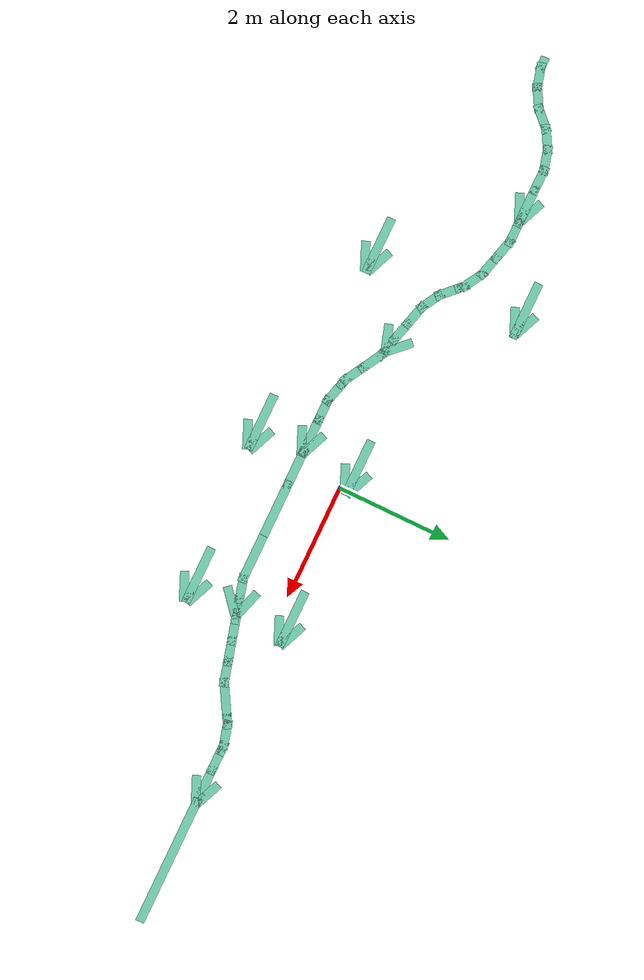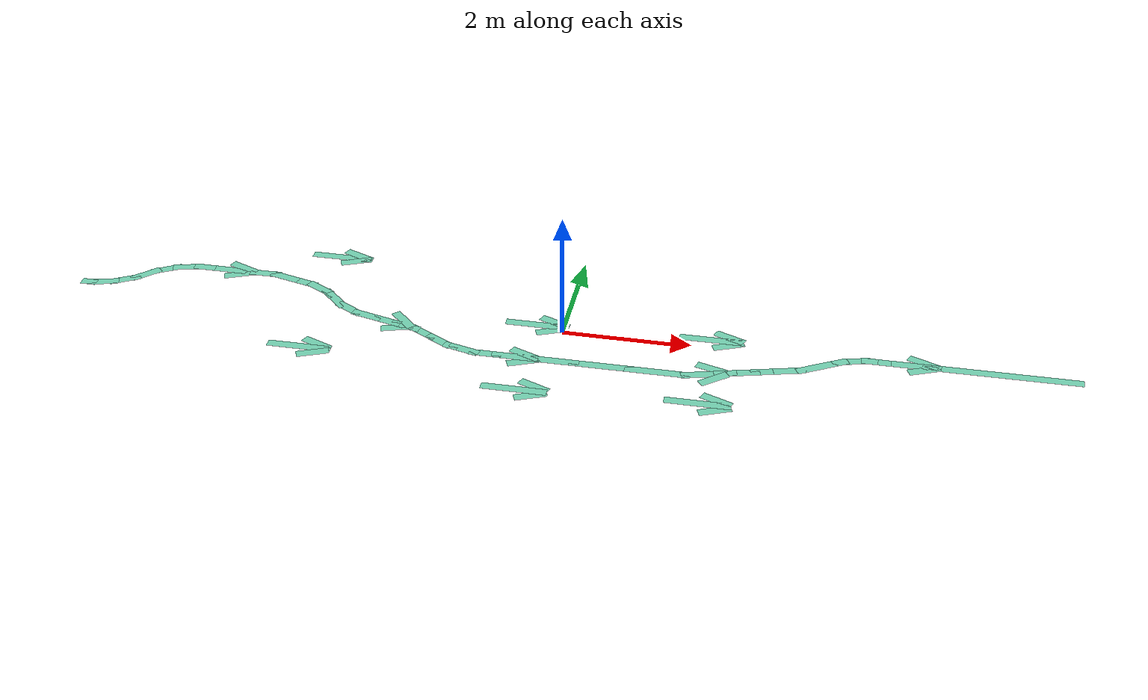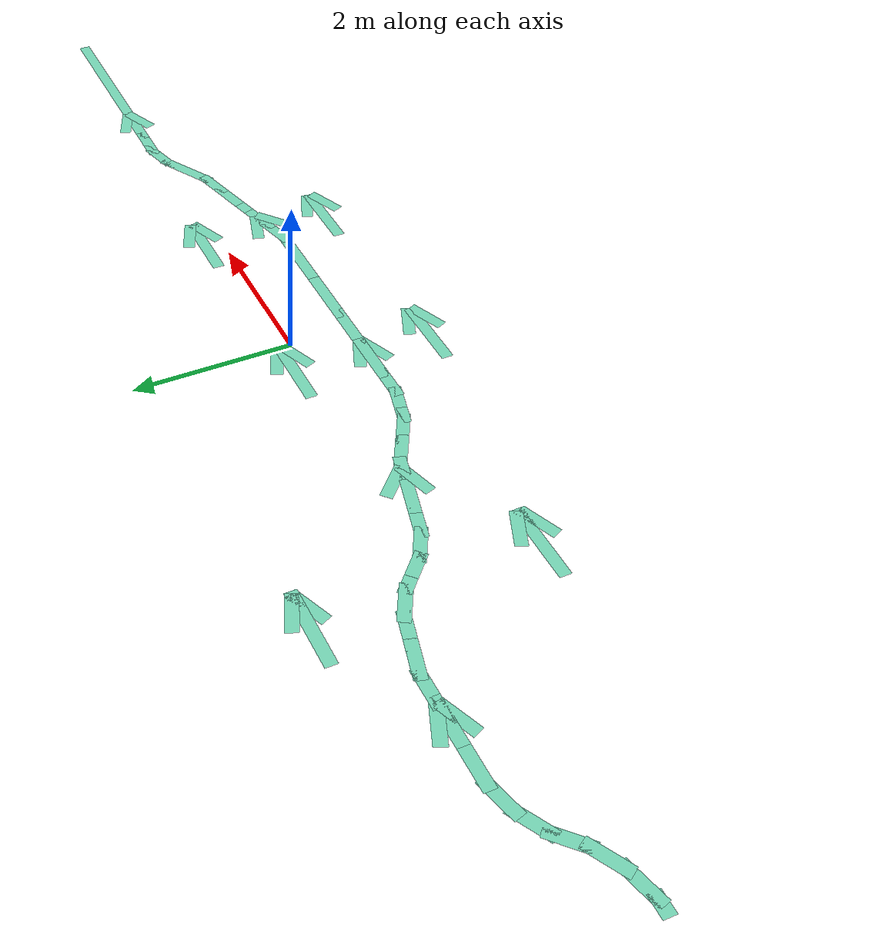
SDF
<?xml version='1.0'?>
<sdf version='1.6'>
  <model name='path_test'>
    <link name='Wall_15'>
      <pose frame=''>-6.00524 0.7938 0 0 -0 0</pose>
      <self_collide>0</self_collide>
      <enable_wind>0</enable_wind>
      <kinematic>0</kinematic>
      <visual name='Wall_15_Visual'>
        <pose frame=''>0 0 0 0 -0 0</pose>
        <geometry>
          <box>
            <size>0.5 0.15 0</size>
          </box>
        </geometry>
        <material>
          <script>
            <uri>file://media/materials/scripts/gazebo.material</uri>
            <name>Gazebo/Grey</name>
          </script>
          <ambient>0.435294 0.796078 0.67451 1</ambient>
          <shader type='pixel'/>
        </material>
        <meta>
          <layer>0</layer>
        </meta>
        <transparency>0</transparency>
        <cast_shadows>1</cast_shadows>
      </visual>
      <collision name='Wall_15_Collision'>
        <laser_retro>0</laser_retro>
        <max_contacts>10</max_contacts>
        <pose frame=''>0 0 0 0 -0 0</pose>
        <geometry>
          <box>
            <size>0.5 0.15 0</size>
          </box>
        </geometry>
        <surface>
          <friction>
            <ode>
              <mu>1</mu>
              <mu2>1</mu2>
              <fdir1>0 0 0</fdir1>
              <slip1>0</slip1>
              <slip2>0</slip2>
            </ode>
            <torsional>
              <coefficient>1</coefficient>
              <patch_radius>0</patch_radius>
              <surface_radius>0</surface_radius>
              <use_patch_radius>1</use_patch_radius>
              <ode>
                <slip>0</slip>
              </ode>
            </torsional>
          </friction>
          <bounce>
            <restitution_coefficient>0</restitution_coefficient>
            <threshold>1e+06</threshold>
          </bounce>
          <contact>
            <collide_without_contact>0</collide_without_contact>
            <collide_without_contact_bitmask>1</collide_without_contact_bitmask>
            <collide_bitmask>1</collide_bitmask>
            <ode>
              <soft_cfm>0</soft_cfm>
              <soft_erp>0.2</soft_erp>
              <kp>1e+13</kp>
              <kd>1</kd>
              <max_vel>0.01</max_vel>
              <min_depth>0</min_depth>
            </ode>
            <bullet>
              <split_impulse>1</split_impulse>
              <split_impulse_penetration_threshold>-0.01</split_impulse_penetration_threshold>
              <soft_cfm>0</soft_cfm>
              <soft_erp>0.2</soft_erp>
              <kp>1e+13</kp>
              <kd>1</kd>
            </bullet>
          </contact>
        </surface>
      </collision>
    </link>
    <link name='Wall_16'>
      <pose frame=''>-5.53024 0.7938 0 0 -0 0</pose>
      <self_collide>0</self_collide>
      <enable_wind>0</enable_wind>
      <kinematic>0</kinematic>
      <visual name='Wall_16_Visual'>
        <pose frame=''>0 0 0 0 -0 0</pose>
        <geometry>
          <box>
            <size>0.75 0.15 0</size>
          </box>
        </geometry>
        <material>
          <script>
            <uri>file://media/materials/scripts/gazebo.material</uri>
            <name>Gazebo/Grey</name>
          </script>
          <ambient>0.435294 0.796078 0.67451 1</ambient>
          <shader type='pixel'/>
        </material>
        <meta>
          <layer>0</layer>
        </meta>
        <transparency>0</transparency>
        <cast_shadows>1</cast_shadows>
      </visual>
      <collision name='Wall_16_Collision'>
        <laser_retro>0</laser_retro>
        <max_contacts>10</max_contacts>
        <pose frame=''>0 0 0 0 -0 0</pose>
        <geometry>
          <box>
            <size>0.75 0.15 0</size>
          </box>
        </geometry>
        <surface>
          <friction>
            <ode>
              <mu>1</mu>
              <mu2>1</mu2>
              <fdir1>0 0 0</fdir1>
              <slip1>0</slip1>
              <slip2>0</slip2>
            </ode>
            <torsional>
              <coefficient>1</coefficient>
              <patch_radius>0</patch_radius>
              <surface_radius>0</surface_radius>
              <use_patch_radius>1</use_patch_radius>
              <ode>
                <slip>0</slip>
              </ode>
            </torsional>
          </friction>
          <bounce>
            <restitution_coefficient>0</restitution_coefficient>
            <threshold>1e+06</threshold>
          </bounce>
          <contact>
            <collide_without_contact>0</collide_without_contact>
            <collide_without_contact_bitmask>1</collide_without_contact_bitmask>
            <collide_bitmask>1</collide_bitmask>
            <ode>
              <soft_cfm>0</soft_cfm>
              <soft_erp>0.2</soft_erp>
              <kp>1e+13</kp>
              <kd>1</kd>
              <max_vel>0.01</max_vel>
              <min_depth>0</min_depth>
            </ode>
            <bullet>
              <split_impulse>1</split_impulse>
              <split_impulse_penetration_threshold>-0.01</split_impulse_penetration_threshold>
              <soft_cfm>0</soft_cfm>
              <soft_erp>0.2</soft_erp>
              <kp>1e+13</kp>
              <kd>1</kd>
            </bullet>
          </contact>
        </surface>
      </collision>
    </link>
    <link name='Wall_17'>
      <pose frame=''>-5.05524 0.7938 0 0 -0 0</pose>
      <self_collide>0</self_collide>
      <enable_wind>0</enable_wind>
      <kinematic>0</kinematic>
      <visual name='Wall_17_Visual'>
        <pose frame=''>0 0 0 0 -0 0</pose>
        <geometry>
          <box>
            <size>0.5 0.15 0</size>
          </box>
        </geometry>
        <material>
          <script>
            <uri>file://media/materials/scripts/gazebo.material</uri>
            <name>Gazebo/Grey</name>
          </script>
          <ambient>0.435294 0.796078 0.67451 1</ambient>
          <shader type='pixel'/>
        </material>
        <meta>
          <layer>0</layer>
        </meta>
        <transparency>0</transparency>
        <cast_shadows>1</cast_shadows>
      </visual>
      <collision name='Wall_17_Collision'>
        <laser_retro>0</laser_retro>
        <max_contacts>10</max_contacts>
        <pose frame=''>0 0 0 0 -0 0</pose>
        <geometry>
          <box>
            <size>0.5 0.15 0</size>
          </box>
        </geometry>
        <surface>
          <friction>
            <ode>
              <mu>1</mu>
              <mu2>1</mu2>
              <fdir1>0 0 0</fdir1>
              <slip1>0</slip1>
              <slip2>0</slip2>
            </ode>
            <torsional>
              <coefficient>1</coefficient>
              <patch_radius>0</patch_radius>
              <surface_radius>0</surface_radius>
              <use_patch_radius>1</use_patch_radius>
              <ode>
                <slip>0</slip>
              </ode>
            </torsional>
          </friction>
          <bounce>
            <restitution_coefficient>0</restitution_coefficient>
            <threshold>1e+06</threshold>
          </bounce>
          <contact>
            <collide_without_contact>0</collide_without_contact>
            <collide_without_contact_bitmask>1</collide_without_contact_bitmask>
            <collide_bitmask>1</collide_bitmask>
            <ode>
              <soft_cfm>0</soft_cfm>
              <soft_erp>0.2</soft_erp>
              <kp>1e+13</kp>
              <kd>1</kd>
              <max_vel>0.01</max_vel>
              <min_depth>0</min_depth>
            </ode>
            <bullet>
              <split_impulse>1</split_impulse>
              <split_impulse_penetration_threshold>-0.01</split_impulse_penetration_threshold>
              <soft_cfm>0</soft_cfm>
              <soft_erp>0.2</soft_erp>
              <kp>1e+13</kp>
              <kd>1</kd>
            </bullet>
          </contact>
        </surface>
      </collision>
    </link>
    <link name='Wall_18'>
      <pose frame=''>-4.7112 0.748507 0 0 0 -0.261799</pose>
      <self_collide>0</self_collide>
      <enable_wind>0</enable_wind>
      <kinematic>0</kinematic>
      <visual name='Wall_18_Visual'>
        <pose frame=''>0 0 0 0 -0 0</pose>
        <geometry>
          <box>
            <size>0.5 0.15 0</size>
          </box>
        </geometry>
        <material>
          <script>
            <uri>file://media/materials/scripts/gazebo.material</uri>
            <name>Gazebo/Grey</name>
          </script>
          <ambient>0.435294 0.796078 0.67451 1</ambient>
          <shader type='pixel'/>
        </material>
        <meta>
          <layer>0</layer>
        </meta>
        <transparency>0</transparency>
        <cast_shadows>1</cast_shadows>
      </visual>
      <collision name='Wall_18_Collision'>
        <laser_retro>0</laser_retro>
        <max_contacts>10</max_contacts>
        <pose frame=''>0 0 0 0 -0 0</pose>
        <geometry>
          <box>
            <size>0.5 0.15 0</size>
          </box>
        </geometry>
        <surface>
          <friction>
            <ode>
              <mu>1</mu>
              <mu2>1</mu2>
              <fdir1>0 0 0</fdir1>
              <slip1>0</slip1>
              <slip2>0</slip2>
            </ode>
            <torsional>
              <coefficient>1</coefficient>
              <patch_radius>0</patch_radius>
              <surface_radius>0</surface_radius>
              <use_patch_radius>1</use_patch_radius>
              <ode>
                <slip>0</slip>
              </ode>
            </torsional>
          </friction>
          <bounce>
            <restitution_coefficient>0</restitution_coefficient>
            <threshold>1e+06</threshold>
          </bounce>
          <contact>
            <collide_without_contact>0</collide_without_contact>
            <collide_without_contact_bitmask>1</collide_without_contact_bitmask>
            <collide_bitmask>1</collide_bitmask>
            <ode>
              <soft_cfm>0</soft_cfm>
              <soft_erp>0.2</soft_erp>
              <kp>1e+13</kp>
              <kd>1</kd>
              <max_vel>0.01</max_vel>
              <min_depth>0</min_depth>
            </ode>
            <bullet>
              <split_impulse>1</split_impulse>
              <split_impulse_penetration_threshold>-0.01</split_impulse_penetration_threshold>
              <soft_cfm>0</soft_cfm>
              <soft_erp>0.2</soft_erp>
              <kp>1e+13</kp>
              <kd>1</kd>
            </bullet>
          </contact>
        </surface>
      </collision>
    </link>
    <link name='Wall_19'>
      <pose frame=''>-4.37313 0.65792 0 0 0 -0.261799</pose>
      <self_collide>0</self_collide>
      <enable_wind>0</enable_wind>
      <kinematic>0</kinematic>
      <visual name='Wall_19_Visual'>
        <pose frame=''>0 0 0 0 -0 0</pose>
        <geometry>
          <box>
            <size>0.5 0.15 0</size>
          </box>
        </geometry>
        <material>
          <script>
            <uri>file://media/materials/scripts/gazebo.material</uri>
            <name>Gazebo/Grey</name>
          </script>
          <ambient>0.435294 0.796078 0.67451 1</ambient>
          <shader type='pixel'/>
        </material>
        <meta>
          <layer>0</layer>
        </meta>
        <transparency>0</transparency>
        <cast_shadows>1</cast_shadows>
      </visual>
      <collision name='Wall_19_Collision'>
        <laser_retro>0</laser_retro>
        <max_contacts>10</max_contacts>
        <pose frame=''>0 0 0 0 -0 0</pose>
        <geometry>
          <box>
            <size>0.5 0.15 0</size>
          </box>
        </geometry>
        <surface>
          <friction>
            <ode>
              <mu>1</mu>
              <mu2>1</mu2>
              <fdir1>0 0 0</fdir1>
              <slip1>0</slip1>
              <slip2>0</slip2>
            </ode>
            <torsional>
              <coefficient>1</coefficient>
              <patch_radius>0</patch_radius>
              <surface_radius>0</surface_radius>
              <use_patch_radius>1</use_patch_radius>
              <ode>
                <slip>0</slip>
              </ode>
            </torsional>
          </friction>
          <bounce>
            <restitution_coefficient>0</restitution_coefficient>
            <threshold>1e+06</threshold>
          </bounce>
          <contact>
            <collide_without_contact>0</collide_without_contact>
            <collide_without_contact_bitmask>1</collide_without_contact_bitmask>
            <collide_bitmask>1</collide_bitmask>
            <ode>
              <soft_cfm>0</soft_cfm>
              <soft_erp>0.2</soft_erp>
              <kp>1e+13</kp>
              <kd>1</kd>
              <max_vel>0.01</max_vel>
              <min_depth>0</min_depth>
            </ode>
            <bullet>
              <split_impulse>1</split_impulse>
              <split_impulse_penetration_threshold>-0.01</split_impulse_penetration_threshold>
              <soft_cfm>0</soft_cfm>
              <soft_erp>0.2</soft_erp>
              <kp>1e+13</kp>
              <kd>1</kd>
            </bullet>
          </contact>
        </surface>
      </collision>
    </link>
    <link name='Wall_20'>
      <pose frame=''>-4.05254 0.525126 0 0 0 -0.523599</pose>
      <self_collide>0</self_collide>
      <enable_wind>0</enable_wind>
      <kinematic>0</kinematic>
      <visual name='Wall_20_Visual'>
        <pose frame=''>0 0 0 0 -0 0</pose>
        <geometry>
          <box>
            <size>0.5 0.15 0</size>
          </box>
        </geometry>
        <material>
          <script>
            <uri>file://media/materials/scripts/gazebo.material</uri>
            <name>Gazebo/Grey</name>
          </script>
          <ambient>0.435294 0.796078 0.67451 1</ambient>
          <shader type='pixel'/>
        </material>
        <meta>
          <layer>0</layer>
        </meta>
        <transparency>0</transparency>
        <cast_shadows>1</cast_shadows>
      </visual>
      <collision name='Wall_20_Collision'>
        <laser_retro>0</laser_retro>
        <max_contacts>10</max_contacts>
        <pose frame=''>0 0 0 0 -0 0</pose>
        <geometry>
          <box>
            <size>0.5 0.15 0</size>
          </box>
        </geometry>
        <surface>
          <friction>
            <ode>
              <mu>1</mu>
              <mu2>1</mu2>
              <fdir1>0 0 0</fdir1>
              <slip1>0</slip1>
              <slip2>0</slip2>
            </ode>
            <torsional>
              <coefficient>1</coefficient>
              <patch_radius>0</patch_radius>
              <surface_radius>0</surface_radius>
              <use_patch_radius>1</use_patch_radius>
              <ode>
                <slip>0</slip>
              </ode>
            </torsional>
          </friction>
          <bounce>
            <restitution_coefficient>0</restitution_coefficient>
            <threshold>1e+06</threshold>
          </bounce>
          <contact>
            <collide_without_contact>0</collide_without_contact>
            <collide_without_contact_bitmask>1</collide_without_contact_bitmask>
            <collide_bitmask>1</collide_bitmask>
            <ode>
              <soft_cfm>0</soft_cfm>
              <soft_erp>0.2</soft_erp>
              <kp>1e+13</kp>
              <kd>1</kd>
              <max_vel>0.01</max_vel>
              <min_depth>0</min_depth>
            </ode>
            <bullet>
              <split_impulse>1</split_impulse>
              <split_impulse_penetration_threshold>-0.01</split_impulse_penetration_threshold>
              <soft_cfm>0</soft_cfm>
              <soft_erp>0.2</soft_erp>
              <kp>1e+13</kp>
              <kd>1</kd>
            </bullet>
          </contact>
        </surface>
      </collision>
    </link>
    <link name='Wall_21'>
      <pose frame=''>-3.86563 0.402271 0 0 0 -0.785398</pose>
      <self_collide>0</self_collide>
      <enable_wind>0</enable_wind>
      <kinematic>0</kinematic>
      <visual name='Wall_21_Visual'>
        <pose frame=''>0 0 0 0 -0 0</pose>
        <geometry>
          <box>
            <size>0.25 0.15 0</size>
          </box>
        </geometry>
        <material>
          <script>
            <uri>file://media/materials/scripts/gazebo.material</uri>
            <name>Gazebo/Grey</name>
          </script>
          <ambient>0.435294 0.796078 0.67451 1</ambient>
          <shader type='pixel'/>
        </material>
        <meta>
          <layer>0</layer>
        </meta>
        <transparency>0</transparency>
        <cast_shadows>1</cast_shadows>
      </visual>
      <collision name='Wall_21_Collision'>
        <laser_retro>0</laser_retro>
        <max_contacts>10</max_contacts>
        <pose frame=''>0 0 0 0 -0 0</pose>
        <geometry>
          <box>
            <size>0.25 0.15 0</size>
          </box>
        </geometry>
        <surface>
          <friction>
            <ode>
              <mu>1</mu>
              <mu2>1</mu2>
              <fdir1>0 0 0</fdir1>
              <slip1>0</slip1>
              <slip2>0</slip2>
            </ode>
            <torsional>
              <coefficient>1</coefficient>
              <patch_radius>0</patch_radius>
              <surface_radius>0</surface_radius>
              <use_patch_radius>1</use_patch_radius>
              <ode>
                <slip>0</slip>
              </ode>
            </torsional>
          </friction>
          <bounce>
            <restitution_coefficient>0</restitution_coefficient>
            <threshold>1e+06</threshold>
          </bounce>
          <contact>
            <collide_without_contact>0</collide_without_contact>
            <collide_without_contact_bitmask>1</collide_without_contact_bitmask>
            <collide_bitmask>1</collide_bitmask>
            <ode>
              <soft_cfm>0</soft_cfm>
              <soft_erp>0.2</soft_erp>
              <kp>1e+13</kp>
              <kd>1</kd>
              <max_vel>0.01</max_vel>
              <min_depth>0</min_depth>
            </ode>
            <bullet>
              <split_impulse>1</split_impulse>
              <split_impulse_penetration_threshold>-0.01</split_impulse_penetration_threshold>
              <soft_cfm>0</soft_cfm>
              <soft_erp>0.2</soft_erp>
              <kp>1e+13</kp>
              <kd>1</kd>
            </bullet>
          </contact>
        </surface>
      </collision>
    </link>
    <link name='Wall_22'>
      <pose frame=''>-3.70653 0.243172 0 0 0 -0.785398</pose>
      <self_collide>0</self_collide>
      <enable_wind>0</enable_wind>
      <kinematic>0</kinematic>
      <visual name='Wall_22_Visual'>
        <pose frame=''>0 0 0 0 -0 0</pose>
        <geometry>
          <box>
            <size>0.5 0.15 0</size>
          </box>
        </geometry>
        <material>
          <script>
            <uri>file://media/materials/scripts/gazebo.material</uri>
            <name>Gazebo/Grey</name>
          </script>
          <ambient>0.435294 0.796078 0.67451 1</ambient>
          <shader type='pixel'/>
        </material>
        <meta>
          <layer>0</layer>
        </meta>
        <transparency>0</transparency>
        <cast_shadows>1</cast_shadows>
      </visual>
      <collision name='Wall_22_Collision'>
        <laser_retro>0</laser_retro>
        <max_contacts>10</max_contacts>
        <pose frame=''>0 0 0 0 -0 0</pose>
        <geometry>
          <box>
            <size>0.5 0.15 0</size>
          </box>
        </geometry>
        <surface>
          <friction>
            <ode>
              <mu>1</mu>
              <mu2>1</mu2>
              <fdir1>0 0 0</fdir1>
              <slip1>0</slip1>
              <slip2>0</slip2>
            </ode>
            <torsional>
              <coefficient>1</coefficient>
              <patch_radius>0</patch_radius>
              <surface_radius>0</surface_radius>
              <use_patch_radius>1</use_patch_radius>
              <ode>
                <slip>0</slip>
              </ode>
            </torsional>
          </friction>
          <bounce>
            <restitution_coefficient>0</restitution_coefficient>
            <threshold>1e+06</threshold>
          </bounce>
          <contact>
            <collide_without_contact>0</collide_without_contact>
            <collide_without_contact_bitmask>1</collide_without_contact_bitmask>
            <collide_bitmask>1</collide_bitmask>
            <ode>
              <soft_cfm>0</soft_cfm>
              <soft_erp>0.2</soft_erp>
              <kp>1e+13</kp>
              <kd>1</kd>
              <max_vel>0.01</max_vel>
              <min_depth>0</min_depth>
            </ode>
            <bullet>
              <split_impulse>1</split_impulse>
              <split_impulse_penetration_threshold>-0.01</split_impulse_penetration_threshold>
              <soft_cfm>0</soft_cfm>
              <soft_erp>0.2</soft_erp>
              <kp>1e+13</kp>
              <kd>1</kd>
            </bullet>
          </contact>
        </surface>
      </collision>
    </link>
    <link name='Wall_23'>
      <pose frame=''>-3.43123 0.031929 0 0 0 -0.523599</pose>
      <self_collide>0</self_collide>
      <enable_wind>0</enable_wind>
      <kinematic>0</kinematic>
      <visual name='Wall_23_Visual'>
        <pose frame=''>0 0 0 0 -0 0</pose>
        <geometry>
          <box>
            <size>0.5 0.15 0</size>
          </box>
        </geometry>
        <material>
          <script>
            <uri>file://media/materials/scripts/gazebo.material</uri>
            <name>Gazebo/Grey</name>
          </script>
          <ambient>0.435294 0.796078 0.67451 1</ambient>
          <shader type='pixel'/>
        </material>
        <meta>
          <layer>0</layer>
        </meta>
        <transparency>0</transparency>
        <cast_shadows>1</cast_shadows>
      </visual>
      <collision name='Wall_23_Collision'>
        <laser_retro>0</laser_retro>
        <max_contacts>10</max_contacts>
        <pose frame=''>0 0 0 0 -0 0</pose>
        <geometry>
          <box>
            <size>0.5 0.15 0</size>
          </box>
        </geometry>
        <surface>
          <friction>
            <ode>
              <mu>1</mu>
              <mu2>1</mu2>
              <fdir1>0 0 0</fdir1>
              <slip1>0</slip1>
              <slip2>0</slip2>
            </ode>
            <torsional>
              <coefficient>1</coefficient>
              <patch_radius>0</patch_radius>
              <surface_radius>0</surface_radius>
              <use_patch_radius>1</use_patch_radius>
              <ode>
                <slip>0</slip>
              </ode>
            </torsional>
          </friction>
          <bounce>
            <restitution_coefficient>0</restitution_coefficient>
            <threshold>1e+06</threshold>
          </bounce>
          <contact>
            <collide_without_contact>0</collide_without_contact>
            <collide_without_contact_bitmask>1</collide_without_contact_bitmask>
            <collide_bitmask>1</collide_bitmask>
            <ode>
              <soft_cfm>0</soft_cfm>
              <soft_erp>0.2</soft_erp>
              <kp>1e+13</kp>
              <kd>1</kd>
              <max_vel>0.01</max_vel>
              <min_depth>0</min_depth>
            </ode>
            <bullet>
              <split_impulse>1</split_impulse>
              <split_impulse_penetration_threshold>-0.01</split_impulse_penetration_threshold>
              <soft_cfm>0</soft_cfm>
              <soft_erp>0.2</soft_erp>
              <kp>1e+13</kp>
              <kd>1</kd>
            </bullet>
          </contact>
        </surface>
      </collision>
    </link>
    <link name='Wall_24'>
      <pose frame=''>-3.11064 -0.100865 0 0 0 -0.261799</pose>
      <self_collide>0</self_collide>
      <enable_wind>0</enable_wind>
      <kinematic>0</kinematic>
      <visual name='Wall_24_Visual'>
        <pose frame=''>0 0 0 0 -0 0</pose>
        <geometry>
          <box>
            <size>0.5 0.15 0</size>
          </box>
        </geometry>
        <material>
          <script>
            <uri>file://media/materials/scripts/gazebo.material</uri>
            <name>Gazebo/Grey</name>
          </script>
          <ambient>0.435294 0.796078 0.67451 1</ambient>
          <shader type='pixel'/>
        </material>
        <meta>
          <layer>0</layer>
        </meta>
        <transparency>0</transparency>
        <cast_shadows>1</cast_shadows>
      </visual>
      <collision name='Wall_24_Collision'>
        <laser_retro>0</laser_retro>
        <max_contacts>10</max_contacts>
        <pose frame=''>0 0 0 0 -0 0</pose>
        <geometry>
          <box>
            <size>0.5 0.15 0</size>
          </box>
        </geometry>
        <surface>
          <friction>
            <ode>
              <mu>1</mu>
              <mu2>1</mu2>
              <fdir1>0 0 0</fdir1>
              <slip1>0</slip1>
              <slip2>0</slip2>
            </ode>
            <torsional>
              <coefficient>1</coefficient>
              <patch_radius>0</patch_radius>
              <surface_radius>0</surface_radius>
              <use_patch_radius>1</use_patch_radius>
              <ode>
                <slip>0</slip>
              </ode>
            </torsional>
          </friction>
          <bounce>
            <restitution_coefficient>0</restitution_coefficient>
            <threshold>1e+06</threshold>
          </bounce>
          <contact>
            <collide_without_contact>0</collide_without_contact>
            <collide_without_contact_bitmask>1</collide_without_contact_bitmask>
            <collide_bitmask>1</collide_bitmask>
            <ode>
              <soft_cfm>0</soft_cfm>
              <soft_erp>0.2</soft_erp>
              <kp>1e+13</kp>
              <kd>1</kd>
              <max_vel>0.01</max_vel>
              <min_depth>0</min_depth>
            </ode>
            <bullet>
              <split_impulse>1</split_impulse>
              <split_impulse_penetration_threshold>-0.01</split_impulse_penetration_threshold>
              <soft_cfm>0</soft_cfm>
              <soft_erp>0.2</soft_erp>
              <kp>1e+13</kp>
              <kd>1</kd>
            </bullet>
          </contact>
        </surface>
      </collision>
    </link>
    <link name='Wall_25'>
      <pose frame=''>-2.77256 -0.191452 0 0 0 -0.261799</pose>
      <self_collide>0</self_collide>
      <enable_wind>0</enable_wind>
      <kinematic>0</kinematic>
      <visual name='Wall_25_Visual'>
        <pose frame=''>0 0 0 0 -0 0</pose>
        <geometry>
          <box>
            <size>0.5 0.15 0</size>
          </box>
        </geometry>
        <material>
          <script>
            <uri>file://media/materials/scripts/gazebo.material</uri>
            <name>Gazebo/Grey</name>
          </script>
          <ambient>0.435294 0.796078 0.67451 1</ambient>
          <shader type='pixel'/>
        </material>
        <meta>
          <layer>0</layer>
        </meta>
        <transparency>0</transparency>
        <cast_shadows>1</cast_shadows>
      </visual>
      <collision name='Wall_25_Collision'>
        <laser_retro>0</laser_retro>
        <max_contacts>10</max_contacts>
        <pose frame=''>0 0 0 0 -0 0</pose>
        <geometry>
          <box>
            <size>0.5 0.15 0</size>
          </box>
        </geometry>
        <surface>
          <friction>
            <ode>
              <mu>1</mu>
              <mu2>1</mu2>
              <fdir1>0 0 0</fdir1>
              <slip1>0</slip1>
              <slip2>0</slip2>
            </ode>
            <torsional>
              <coefficient>1</coefficient>
              <patch_radius>0</patch_radius>
              <surface_radius>0</surface_radius>
              <use_patch_radius>1</use_patch_radius>
              <ode>
                <slip>0</slip>
              </ode>
            </torsional>
          </friction>
          <bounce>
            <restitution_coefficient>0</restitution_coefficient>
            <threshold>1e+06</threshold>
          </bounce>
          <contact>
            <collide_without_contact>0</collide_without_contact>
            <collide_without_contact_bitmask>1</collide_without_contact_bitmask>
            <collide_bitmask>1</collide_bitmask>
            <ode>
              <soft_cfm>0</soft_cfm>
              <soft_erp>0.2</soft_erp>
              <kp>1e+13</kp>
              <kd>1</kd>
              <max_vel>0.01</max_vel>
              <min_depth>0</min_depth>
            </ode>
            <bullet>
              <split_impulse>1</split_impulse>
              <split_impulse_penetration_threshold>-0.01</split_impulse_penetration_threshold>
              <soft_cfm>0</soft_cfm>
              <soft_erp>0.2</soft_erp>
              <kp>1e+13</kp>
              <kd>1</kd>
            </bullet>
          </contact>
        </surface>
      </collision>
    </link>
    <link name='Wall_27'>
      <pose frame=''>-2.1139 -0.414832 0 0 0 -0.523599</pose>
      <self_collide>0</self_collide>
      <enable_wind>0</enable_wind>
      <kinematic>0</kinematic>
      <visual name='Wall_27_Visual'>
        <pose frame=''>0 0 0 0 -0 0</pose>
        <geometry>
          <box>
            <size>0.5 0.15 0</size>
          </box>
        </geometry>
        <material>
          <script>
            <uri>file://media/materials/scripts/gazebo.material</uri>
            <name>Gazebo/Grey</name>
          </script>
          <ambient>0.435294 0.796078 0.67451 1</ambient>
          <shader type='pixel'/>
        </material>
        <meta>
          <layer>0</layer>
        </meta>
        <transparency>0</transparency>
        <cast_shadows>1</cast_shadows>
      </visual>
      <collision name='Wall_27_Collision'>
        <laser_retro>0</laser_retro>
        <max_contacts>10</max_contacts>
        <pose frame=''>0 0 0 0 -0 0</pose>
        <geometry>
          <box>
            <size>0.5 0.15 0</size>
          </box>
        </geometry>
        <surface>
          <friction>
            <ode>
              <mu>1</mu>
              <mu2>1</mu2>
              <fdir1>0 0 0</fdir1>
              <slip1>0</slip1>
              <slip2>0</slip2>
            </ode>
            <torsional>
              <coefficient>1</coefficient>
              <patch_radius>0</patch_radius>
              <surface_radius>0</surface_radius>
              <use_patch_radius>1</use_patch_radius>
              <ode>
                <slip>0</slip>
              </ode>
            </torsional>
          </friction>
          <bounce>
            <restitution_coefficient>0</restitution_coefficient>
            <threshold>1e+06</threshold>
          </bounce>
          <contact>
            <collide_without_contact>0</collide_without_contact>
            <collide_without_contact_bitmask>1</collide_without_contact_bitmask>
            <collide_bitmask>1</collide_bitmask>
            <ode>
              <soft_cfm>0</soft_cfm>
              <soft_erp>0.2</soft_erp>
              <kp>1e+13</kp>
              <kd>1</kd>
              <max_vel>0.01</max_vel>
              <min_depth>0</min_depth>
            </ode>
            <bullet>
              <split_impulse>1</split_impulse>
              <split_impulse_penetration_threshold>-0.01</split_impulse_penetration_threshold>
              <soft_cfm>0</soft_cfm>
              <soft_erp>0.2</soft_erp>
              <kp>1e+13</kp>
              <kd>1</kd>
            </bullet>
          </contact>
        </surface>
      </collision>
    </link>
    <link name='Wall_28'>
      <pose frame=''>-1.81079 -0.589831 0 0 0 -0.523599</pose>
      <self_collide>0</self_collide>
      <enable_wind>0</enable_wind>
      <kinematic>0</kinematic>
      <visual name='Wall_28_Visual'>
        <pose frame=''>0 0 0 0 -0 0</pose>
        <geometry>
          <box>
            <size>0.5 0.15 0</size>
          </box>
        </geometry>
        <material>
          <script>
            <uri>file://media/materials/scripts/gazebo.material</uri>
            <name>Gazebo/Grey</name>
          </script>
          <ambient>0.435294 0.796078 0.67451 1</ambient>
          <shader type='pixel'/>
        </material>
        <meta>
          <layer>0</layer>
        </meta>
        <transparency>0</transparency>
        <cast_shadows>1</cast_shadows>
      </visual>
      <collision name='Wall_28_Collision'>
        <laser_retro>0</laser_retro>
        <max_contacts>10</max_contacts>
        <pose frame=''>0 0 0 0 -0 0</pose>
        <geometry>
          <box>
            <size>0.5 0.15 0</size>
          </box>
        </geometry>
        <surface>
          <friction>
            <ode>
              <mu>1</mu>
              <mu2>1</mu2>
              <fdir1>0 0 0</fdir1>
              <slip1>0</slip1>
              <slip2>0</slip2>
            </ode>
            <torsional>
              <coefficient>1</coefficient>
              <patch_radius>0</patch_radius>
              <surface_radius>0</surface_radius>
              <use_patch_radius>1</use_patch_radius>
              <ode>
                <slip>0</slip>
              </ode>
            </torsional>
          </friction>
          <bounce>
            <restitution_coefficient>0</restitution_coefficient>
            <threshold>1e+06</threshold>
          </bounce>
          <contact>
            <collide_without_contact>0</collide_without_contact>
            <collide_without_contact_bitmask>1</collide_without_contact_bitmask>
            <collide_bitmask>1</collide_bitmask>
            <ode>
              <soft_cfm>0</soft_cfm>
              <soft_erp>0.2</soft_erp>
              <kp>1e+13</kp>
              <kd>1</kd>
              <max_vel>0.01</max_vel>
              <min_depth>0</min_depth>
            </ode>
            <bullet>
              <split_impulse>1</split_impulse>
              <split_impulse_penetration_threshold>-0.01</split_impulse_penetration_threshold>
              <soft_cfm>0</soft_cfm>
              <soft_erp>0.2</soft_erp>
              <kp>1e+13</kp>
              <kd>1</kd>
            </bullet>
          </contact>
        </surface>
      </collision>
    </link>
    <link name='Wall_29'>
      <pose frame=''>-1.61094 -0.690272 0 0 0 -0.261799</pose>
      <self_collide>0</self_collide>
      <enable_wind>0</enable_wind>
      <kinematic>0</kinematic>
      <visual name='Wall_29_Visual'>
        <pose frame=''>0 0 0 0 -0 0</pose>
        <geometry>
          <box>
            <size>0.25 0.15 0</size>
          </box>
        </geometry>
        <material>
          <script>
            <uri>file://media/materials/scripts/gazebo.material</uri>
            <name>Gazebo/Grey</name>
          </script>
          <ambient>0.435294 0.796078 0.67451 1</ambient>
          <shader type='pixel'/>
        </material>
        <meta>
          <layer>0</layer>
        </meta>
        <transparency>0</transparency>
        <cast_shadows>1</cast_shadows>
      </visual>
      <collision name='Wall_29_Collision'>
        <laser_retro>0</laser_retro>
        <max_contacts>10</max_contacts>
        <pose frame=''>0 0 0 0 -0 0</pose>
        <geometry>
          <box>
            <size>0.25 0.15 0</size>
          </box>
        </geometry>
        <surface>
          <friction>
            <ode>
              <mu>1</mu>
              <mu2>1</mu2>
              <fdir1>0 0 0</fdir1>
              <slip1>0</slip1>
              <slip2>0</slip2>
            </ode>
            <torsional>
              <coefficient>1</coefficient>
              <patch_radius>0</patch_radius>
              <surface_radius>0</surface_radius>
              <use_patch_radius>1</use_patch_radius>
              <ode>
                <slip>0</slip>
              </ode>
            </torsional>
          </friction>
          <bounce>
            <restitution_coefficient>0</restitution_coefficient>
            <threshold>1e+06</threshold>
          </bounce>
          <contact>
            <collide_without_contact>0</collide_without_contact>
            <collide_without_contact_bitmask>1</collide_without_contact_bitmask>
            <collide_bitmask>1</collide_bitmask>
            <ode>
              <soft_cfm>0</soft_cfm>
              <soft_erp>0.2</soft_erp>
              <kp>1e+13</kp>
              <kd>1</kd>
              <max_vel>0.01</max_vel>
              <min_depth>0</min_depth>
            </ode>
            <bullet>
              <split_impulse>1</split_impulse>
              <split_impulse_penetration_threshold>-0.01</split_impulse_penetration_threshold>
              <soft_cfm>0</soft_cfm>
              <soft_erp>0.2</soft_erp>
              <kp>1e+13</kp>
              <kd>1</kd>
            </bullet>
          </contact>
        </surface>
      </collision>
    </link>
    <link name='Wall_30'>
      <pose frame=''>-1.39361 -0.748507 0 0 0 -0.261799</pose>
      <self_collide>0</self_collide>
      <enable_wind>0</enable_wind>
      <kinematic>0</kinematic>
      <visual name='Wall_30_Visual'>
        <pose frame=''>0 0 0 0 -0 0</pose>
        <geometry>
          <box>
            <size>0.5 0.15 0</size>
          </box>
        </geometry>
        <material>
          <script>
            <uri>file://media/materials/scripts/gazebo.material</uri>
            <name>Gazebo/Grey</name>
          </script>
          <ambient>0.435294 0.796078 0.67451 1</ambient>
          <shader type='pixel'/>
        </material>
        <meta>
          <layer>0</layer>
        </meta>
        <transparency>0</transparency>
        <cast_shadows>1</cast_shadows>
      </visual>
      <collision name='Wall_30_Collision'>
        <laser_retro>0</laser_retro>
        <max_contacts>10</max_contacts>
        <pose frame=''>0 0 0 0 -0 0</pose>
        <geometry>
          <box>
            <size>0.5 0.15 0</size>
          </box>
        </geometry>
        <surface>
          <friction>
            <ode>
              <mu>1</mu>
              <mu2>1</mu2>
              <fdir1>0 0 0</fdir1>
              <slip1>0</slip1>
              <slip2>0</slip2>
            </ode>
            <torsional>
              <coefficient>1</coefficient>
              <patch_radius>0</patch_radius>
              <surface_radius>0</surface_radius>
              <use_patch_radius>1</use_patch_radius>
              <ode>
                <slip>0</slip>
              </ode>
            </torsional>
          </friction>
          <bounce>
            <restitution_coefficient>0</restitution_coefficient>
            <threshold>1e+06</threshold>
          </bounce>
          <contact>
            <collide_without_contact>0</collide_without_contact>
            <collide_without_contact_bitmask>1</collide_without_contact_bitmask>
            <collide_bitmask>1</collide_bitmask>
            <ode>
              <soft_cfm>0</soft_cfm>
              <soft_erp>0.2</soft_erp>
              <kp>1e+13</kp>
              <kd>1</kd>
              <max_vel>0.01</max_vel>
              <min_depth>0</min_depth>
            </ode>
            <bullet>
              <split_impulse>1</split_impulse>
              <split_impulse_penetration_threshold>-0.01</split_impulse_penetration_threshold>
              <soft_cfm>0</soft_cfm>
              <soft_erp>0.2</soft_erp>
              <kp>1e+13</kp>
              <kd>1</kd>
            </bullet>
          </contact>
        </surface>
      </collision>
    </link>
    <link name='Wall_30_clone_clone'>
      <pose frame=''>-5.4542 0.690381 0 0 -0 0.4</pose>
      <self_collide>0</self_collide>
      <enable_wind>0</enable_wind>
      <kinematic>0</kinematic>
      <gravity>1</gravity>
      <inertial>
        <mass>1</mass>
        <pose frame=''>0 0 0 0 -0 0</pose>
        <inertia>
          <ixx>1</ixx>
          <ixy>0</ixy>
          <ixz>0</ixz>
          <iyy>1</iyy>
          <iyz>0</iyz>
          <izz>1</izz>
        </inertia>
      </inertial>
      <visual name='Wall_30_Visual'>
        <pose frame=''>0 0 0 0 -0 0</pose>
        <geometry>
          <box>
            <size>0.5 0.15 0</size>
          </box>
        </geometry>
        <material>
          <script>
            <uri>file://media/materials/scripts/gazebo.material</uri>
            <name>Gazebo/Grey</name>
          </script>
          <ambient>0.435 0.796 0.675 1</ambient>
          <shader type='pixel'>
            <normal_map>__default__</normal_map>
          </shader>
          <diffuse>0.7 0.7 0.7 1</diffuse>
          <specular>0.01 0.01 0.01 1</specular>
          <emissive>0 0 0 1</emissive>
        </material>
        <meta>
          <layer>0</layer>
        </meta>
        <transparency>0</transparency>
        <cast_shadows>1</cast_shadows>
      </visual>
      <collision name='Wall_30_Collision'>
        <laser_retro>0</laser_retro>
        <max_contacts>10</max_contacts>
        <pose frame=''>0 0 0 0 -0 0</pose>
        <geometry>
          <box>
            <size>0.5 0.15 0</size>
          </box>
        </geometry>
        <surface>
          <friction>
            <ode>
              <mu>1</mu>
              <mu2>1</mu2>
              <fdir1>0 0 0</fdir1>
              <slip1>0</slip1>
              <slip2>0</slip2>
            </ode>
            <torsional>
              <coefficient>1</coefficient>
              <patch_radius>0</patch_radius>
              <surface_radius>0</surface_radius>
              <use_patch_radius>1</use_patch_radius>
              <ode>
                <slip>0</slip>
              </ode>
            </torsional>
          </friction>
          <bounce>
            <restitution_coefficient>0</restitution_coefficient>
            <threshold>1e+06</threshold>
          </bounce>
          <contact>
            <collide_without_contact>0</collide_without_contact>
            <collide_without_contact_bitmask>1</collide_without_contact_bitmask>
            <collide_bitmask>1</collide_bitmask>
            <ode>
              <soft_cfm>0</soft_cfm>
              <soft_erp>0.2</soft_erp>
              <kp>1e+13</kp>
              <kd>1</kd>
              <max_vel>0.01</max_vel>
              <min_depth>0</min_depth>
            </ode>
            <bullet>
              <split_impulse>1</split_impulse>
              <split_impulse_penetration_threshold>-0.01</split_impulse_penetration_threshold>
              <soft_cfm>0</soft_cfm>
              <soft_erp>0.2</soft_erp>
              <kp>1e+13</kp>
              <kd>1</kd>
            </bullet>
          </contact>
        </surface>
      </collision>
    </link>
    <link name='Wall_30_clone_clone_0'>
      <pose frame=''>-5.44614 0.892389 0 0 0 -0.4</pose>
      <self_collide>0</self_collide>
      <enable_wind>0</enable_wind>
      <kinematic>0</kinematic>
      <gravity>1</gravity>
      <inertial>
        <mass>1</mass>
        <pose frame=''>0 0 0 0 -0 0</pose>
        <inertia>
          <ixx>1</ixx>
          <ixy>0</ixy>
          <ixz>0</ixz>
          <iyy>1</iyy>
          <iyz>0</iyz>
          <izz>1</izz>
        </inertia>
      </inertial>
      <visual name='Wall_30_Visual'>
        <pose frame=''>0 0 0 0 -0 0</pose>
        <geometry>
          <box>
            <size>0.5 0.15 0</size>
          </box>
        </geometry>
        <material>
          <script>
            <uri>file://media/materials/scripts/gazebo.material</uri>
            <name>Gazebo/Grey</name>
          </script>
          <ambient>0.435 0.796 0.675 1</ambient>
          <shader type='pixel'>
            <normal_map>__default__</normal_map>
          </shader>
          <diffuse>0.7 0.7 0.7 1</diffuse>
          <specular>0.01 0.01 0.01 1</specular>
          <emissive>0 0 0 1</emissive>
        </material>
        <meta>
          <layer>0</layer>
        </meta>
        <transparency>0</transparency>
        <cast_shadows>1</cast_shadows>
      </visual>
      <collision name='Wall_30_Collision'>
        <laser_retro>0</laser_retro>
        <max_contacts>10</max_contacts>
        <pose frame=''>0 0 0 0 -0 0</pose>
        <geometry>
          <box>
            <size>0.5 0.15 0</size>
          </box>
        </geometry>
        <surface>
          <friction>
            <ode>
              <mu>1</mu>
              <mu2>1</mu2>
              <fdir1>0 0 0</fdir1>
              <slip1>0</slip1>
              <slip2>0</slip2>
            </ode>
            <torsional>
              <coefficient>1</coefficient>
              <patch_radius>0</patch_radius>
              <surface_radius>0</surface_radius>
              <use_patch_radius>1</use_patch_radius>
              <ode>
                <slip>0</slip>
              </ode>
            </torsional>
          </friction>
          <bounce>
            <restitution_coefficient>0</restitution_coefficient>
            <threshold>1e+06</threshold>
          </bounce>
          <contact>
            <collide_without_contact>0</collide_without_contact>
            <collide_without_contact_bitmask>1</collide_without_contact_bitmask>
            <collide_bitmask>1</collide_bitmask>
            <ode>
              <soft_cfm>0</soft_cfm>
              <soft_erp>0.2</soft_erp>
              <kp>1e+13</kp>
              <kd>1</kd>
              <max_vel>0.01</max_vel>
              <min_depth>0</min_depth>
            </ode>
            <bullet>
              <split_impulse>1</split_impulse>
              <split_impulse_penetration_threshold>-0.01</split_impulse_penetration_threshold>
              <soft_cfm>0</soft_cfm>
              <soft_erp>0.2</soft_erp>
              <kp>1e+13</kp>
              <kd>1</kd>
            </bullet>
          </contact>
        </surface>
      </collision>
    </link>
    <link name='Wall_30_clone_clone_0_clone'>
      <pose frame=''>-3.7173 1.61571 0 0 0 -0.4</pose>
      <self_collide>0</self_collide>
      <enable_wind>0</enable_wind>
      <kinematic>0</kinematic>
      <gravity>1</gravity>
      <inertial>
        <mass>1</mass>
        <pose frame=''>0 0 0 0 -0 0</pose>
        <inertia>
          <ixx>1</ixx>
          <ixy>0</ixy>
          <ixz>0</ixz>
          <iyy>1</iyy>
          <iyz>0</iyz>
          <izz>1</izz>
        </inertia>
      </inertial>
      <visual name='Wall_30_Visual'>
        <pose frame=''>0 0 0 0 -0 0</pose>
        <geometry>
          <box>
            <size>0.5 0.15 0</size>
          </box>
        </geometry>
        <material>
          <script>
            <uri>file://media/materials/scripts/gazebo.material</uri>
            <name>Gazebo/Grey</name>
          </script>
          <ambient>0.435 0.796 0.675 1</ambient>
          <shader type='pixel'>
            <normal_map>__default__</normal_map>
          </shader>
          <diffuse>0.7 0.7 0.7 1</diffuse>
          <specular>0.01 0.01 0.01 1</specular>
          <emissive>0 0 0 1</emissive>
        </material>
        <meta>
          <layer>0</layer>
        </meta>
        <transparency>0</transparency>
        <cast_shadows>1</cast_shadows>
      </visual>
      <collision name='Wall_30_Collision'>
        <laser_retro>0</laser_retro>
        <max_contacts>10</max_contacts>
        <pose frame=''>0 0 0 0 -0 0</pose>
        <geometry>
          <box>
            <size>0.5 0.15 0</size>
          </box>
        </geometry>
        <surface>
          <friction>
            <ode>
              <mu>1</mu>
              <mu2>1</mu2>
              <fdir1>0 0 0</fdir1>
              <slip1>0</slip1>
              <slip2>0</slip2>
            </ode>
            <torsional>
              <coefficient>1</coefficient>
              <patch_radius>0</patch_radius>
              <surface_radius>0</surface_radius>
              <use_patch_radius>1</use_patch_radius>
              <ode>
                <slip>0</slip>
              </ode>
            </torsional>
          </friction>
          <bounce>
            <restitution_coefficient>0</restitution_coefficient>
            <threshold>1e+06</threshold>
          </bounce>
          <contact>
            <collide_without_contact>0</collide_without_contact>
            <collide_without_contact_bitmask>1</collide_without_contact_bitmask>
            <collide_bitmask>1</collide_bitmask>
            <ode>
              <soft_cfm>0</soft_cfm>
              <soft_erp>0.2</soft_erp>
              <kp>1e+13</kp>
              <kd>1</kd>
              <max_vel>0.01</max_vel>
              <min_depth>0</min_depth>
            </ode>
            <bullet>
              <split_impulse>1</split_impulse>
              <split_impulse_penetration_threshold>-0.01</split_impulse_penetration_threshold>
              <soft_cfm>0</soft_cfm>
              <soft_erp>0.2</soft_erp>
              <kp>1e+13</kp>
              <kd>1</kd>
            </bullet>
          </contact>
        </surface>
      </collision>
    </link>
    <link name='Wall_30_clone_clone_0_clone_0_clone'>
      <pose frame=''>-2.5096 -0.121844 0 0 0 -0.8</pose>
      <self_collide>0</self_collide>
      <enable_wind>0</enable_wind>
      <kinematic>0</kinematic>
      <gravity>1</gravity>
      <inertial>
        <mass>1</mass>
        <pose frame=''>0 0 0 0 -0 0</pose>
        <inertia>
          <ixx>1</ixx>
          <ixy>0</ixy>
          <ixz>0</ixz>
          <iyy>1</iyy>
          <iyz>0</iyz>
          <izz>1</izz>
        </inertia>
      </inertial>
      <visual name='Wall_30_Visual'>
        <pose frame=''>0 0 0 0 -0 0</pose>
        <geometry>
          <box>
            <size>0.5 0.15 0</size>
          </box>
        </geometry>
        <material>
          <script>
            <uri>file://media/materials/scripts/gazebo.material</uri>
            <name>Gazebo/Grey</name>
          </script>
          <ambient>0.435 0.796 0.675 1</ambient>
          <shader type='pixel'>
            <normal_map>__default__</normal_map>
          </shader>
          <diffuse>0.7 0.7 0.7 1</diffuse>
          <specular>0.01 0.01 0.01 1</specular>
          <emissive>0 0 0 1</emissive>
        </material>
        <meta>
          <layer>0</layer>
        </meta>
        <transparency>0</transparency>
        <cast_shadows>1</cast_shadows>
      </visual>
      <collision name='Wall_30_Collision'>
        <laser_retro>0</laser_retro>
        <max_contacts>10</max_contacts>
        <pose frame=''>0 0 0 0 -0 0</pose>
        <geometry>
          <box>
            <size>0.5 0.15 0</size>
          </box>
        </geometry>
        <surface>
          <friction>
            <ode>
              <mu>1</mu>
              <mu2>1</mu2>
              <fdir1>0 0 0</fdir1>
              <slip1>0</slip1>
              <slip2>0</slip2>
            </ode>
            <torsional>
              <coefficient>1</coefficient>
              <patch_radius>0</patch_radius>
              <surface_radius>0</surface_radius>
              <use_patch_radius>1</use_patch_radius>
              <ode>
                <slip>0</slip>
              </ode>
            </torsional>
          </friction>
          <bounce>
            <restitution_coefficient>0</restitution_coefficient>
            <threshold>1e+06</threshold>
          </bounce>
          <contact>
            <collide_without_contact>0</collide_without_contact>
            <collide_without_contact_bitmask>1</collide_without_contact_bitmask>
            <collide_bitmask>1</collide_bitmask>
            <ode>
              <soft_cfm>0</soft_cfm>
              <soft_erp>0.2</soft_erp>
              <kp>1e+13</kp>
              <kd>1</kd>
              <max_vel>0.01</max_vel>
              <min_depth>0</min_depth>
            </ode>
            <bullet>
              <split_impulse>1</split_impulse>
              <split_impulse_penetration_threshold>-0.01</split_impulse_penetration_threshold>
              <soft_cfm>0</soft_cfm>
              <soft_erp>0.2</soft_erp>
              <kp>1e+13</kp>
              <kd>1</kd>
            </bullet>
          </contact>
        </surface>
      </collision>
    </link>
    <link name='Wall_30_clone_clone_0_clone_0_clone_0'>
      <pose frame=''>-2.55941 -0.352224 0 0 -0 0.3</pose>
      <self_collide>0</self_collide>
      <enable_wind>0</enable_wind>
      <kinematic>0</kinematic>
      <gravity>1</gravity>
      <inertial>
        <mass>1</mass>
        <pose frame=''>0 0 0 0 -0 0</pose>
        <inertia>
          <ixx>1</ixx>
          <ixy>0</ixy>
          <ixz>0</ixz>
          <iyy>1</iyy>
          <iyz>0</iyz>
          <izz>1</izz>
        </inertia>
      </inertial>
      <visual name='Wall_30_Visual'>
        <pose frame=''>0 0 0 0 -0 0</pose>
        <geometry>
          <box>
            <size>0.5 0.15 0</size>
          </box>
        </geometry>
        <material>
          <script>
            <uri>file://media/materials/scripts/gazebo.material</uri>
            <name>Gazebo/Grey</name>
          </script>
          <ambient>0.435 0.796 0.675 1</ambient>
          <shader type='pixel'>
            <normal_map>__default__</normal_map>
          </shader>
          <diffuse>0.7 0.7 0.7 1</diffuse>
          <specular>0.01 0.01 0.01 1</specular>
          <emissive>0 0 0 1</emissive>
        </material>
        <meta>
          <layer>0</layer>
        </meta>
        <transparency>0</transparency>
        <cast_shadows>1</cast_shadows>
      </visual>
      <collision name='Wall_30_Collision'>
        <laser_retro>0</laser_retro>
        <max_contacts>10</max_contacts>
        <pose frame=''>0 0 0 0 -0 0</pose>
        <geometry>
          <box>
            <size>0.5 0.15 0</size>
          </box>
        </geometry>
        <surface>
          <friction>
            <ode>
              <mu>1</mu>
              <mu2>1</mu2>
              <fdir1>0 0 0</fdir1>
              <slip1>0</slip1>
              <slip2>0</slip2>
            </ode>
            <torsional>
              <coefficient>1</coefficient>
              <patch_radius>0</patch_radius>
              <surface_radius>0</surface_radius>
              <use_patch_radius>1</use_patch_radius>
              <ode>
                <slip>0</slip>
              </ode>
            </torsional>
          </friction>
          <bounce>
            <restitution_coefficient>0</restitution_coefficient>
            <threshold>1e+06</threshold>
          </bounce>
          <contact>
            <collide_without_contact>0</collide_without_contact>
            <collide_without_contact_bitmask>1</collide_without_contact_bitmask>
            <collide_bitmask>1</collide_bitmask>
            <ode>
              <soft_cfm>0</soft_cfm>
              <soft_erp>0.2</soft_erp>
              <kp>1e+13</kp>
              <kd>1</kd>
              <max_vel>0.01</max_vel>
              <min_depth>0</min_depth>
            </ode>
            <bullet>
              <split_impulse>1</split_impulse>
              <split_impulse_penetration_threshold>-0.01</split_impulse_penetration_threshold>
              <soft_cfm>0</soft_cfm>
              <soft_erp>0.2</soft_erp>
              <kp>1e+13</kp>
              <kd>1</kd>
            </bullet>
          </contact>
        </surface>
      </collision>
    </link>
    <link name='Wall_30_clone_clone_0_clone_clone'>
      <pose frame=''>-3.6409 -1.02093 0 0 0 -0.4</pose>
      <self_collide>0</self_collide>
      <enable_wind>0</enable_wind>
      <kinematic>0</kinematic>
      <gravity>1</gravity>
      <inertial>
        <mass>1</mass>
        <pose frame=''>0 0 0 0 -0 0</pose>
        <inertia>
          <ixx>1</ixx>
          <ixy>0</ixy>
          <ixz>0</ixz>
          <iyy>1</iyy>
          <iyz>0</iyz>
          <izz>1</izz>
        </inertia>
      </inertial>
      <visual name='Wall_30_Visual'>
        <pose frame=''>0 0 0 0 -0 0</pose>
        <geometry>
          <box>
            <size>0.5 0.15 0</size>
          </box>
        </geometry>
        <material>
          <script>
            <uri>file://media/materials/scripts/gazebo.material</uri>
            <name>Gazebo/Grey</name>
          </script>
          <ambient>0.435 0.796 0.675 1</ambient>
          <shader type='pixel'>
            <normal_map>__default__</normal_map>
          </shader>
          <diffuse>0.7 0.7 0.7 1</diffuse>
          <specular>0.01 0.01 0.01 1</specular>
          <emissive>0 0 0 1</emissive>
        </material>
        <meta>
          <layer>0</layer>
        </meta>
        <transparency>0</transparency>
        <cast_shadows>1</cast_shadows>
      </visual>
      <collision name='Wall_30_Collision'>
        <laser_retro>0</laser_retro>
        <max_contacts>10</max_contacts>
        <pose frame=''>0 0 0 0 -0 0</pose>
        <geometry>
          <box>
            <size>0.5 0.15 0</size>
          </box>
        </geometry>
        <surface>
          <friction>
            <ode>
              <mu>1</mu>
              <mu2>1</mu2>
              <fdir1>0 0 0</fdir1>
              <slip1>0</slip1>
              <slip2>0</slip2>
            </ode>
            <torsional>
              <coefficient>1</coefficient>
              <patch_radius>0</patch_radius>
              <surface_radius>0</surface_radius>
              <use_patch_radius>1</use_patch_radius>
              <ode>
                <slip>0</slip>
              </ode>
            </torsional>
          </friction>
          <bounce>
            <restitution_coefficient>0</restitution_coefficient>
            <threshold>1e+06</threshold>
          </bounce>
          <contact>
            <collide_without_contact>0</collide_without_contact>
            <collide_without_contact_bitmask>1</collide_without_contact_bitmask>
            <collide_bitmask>1</collide_bitmask>
            <ode>
              <soft_cfm>0</soft_cfm>
              <soft_erp>0.2</soft_erp>
              <kp>1e+13</kp>
              <kd>1</kd>
              <max_vel>0.01</max_vel>
              <min_depth>0</min_depth>
            </ode>
            <bullet>
              <split_impulse>1</split_impulse>
              <split_impulse_penetration_threshold>-0.01</split_impulse_penetration_threshold>
              <soft_cfm>0</soft_cfm>
              <soft_erp>0.2</soft_erp>
              <kp>1e+13</kp>
              <kd>1</kd>
            </bullet>
          </contact>
        </surface>
      </collision>
    </link>
    <link name='Wall_30_clone_clone_0_clone_clone_0_clone'>
      <pose frame=''>-0.171138 0.256709 0 0 0 -0.4</pose>
      <self_collide>0</self_collide>
      <enable_wind>0</enable_wind>
      <kinematic>0</kinematic>
      <gravity>1</gravity>
      <inertial>
        <mass>1</mass>
        <pose frame=''>0 0 0 0 -0 0</pose>
        <inertia>
          <ixx>1</ixx>
          <ixy>0</ixy>
          <ixz>0</ixz>
          <iyy>1</iyy>
          <iyz>0</iyz>
          <izz>1</izz>
        </inertia>
      </inertial>
      <visual name='Wall_30_Visual'>
        <pose frame=''>0 0 0 0 -0 0</pose>
        <geometry>
          <box>
            <size>0.5 0.15 0</size>
          </box>
        </geometry>
        <material>
          <script>
            <uri>file://media/materials/scripts/gazebo.material</uri>
            <name>Gazebo/Grey</name>
          </script>
          <ambient>0.435 0.796 0.675 1</ambient>
          <shader type='pixel'>
            <normal_map>__default__</normal_map>
          </shader>
          <diffuse>0.7 0.7 0.7 1</diffuse>
          <specular>0.01 0.01 0.01 1</specular>
          <emissive>0 0 0 1</emissive>
        </material>
        <meta>
          <layer>0</layer>
        </meta>
        <transparency>0</transparency>
        <cast_shadows>1</cast_shadows>
      </visual>
      <collision name='Wall_30_Collision'>
        <laser_retro>0</laser_retro>
        <max_contacts>10</max_contacts>
        <pose frame=''>0 0 0 0 -0 0</pose>
        <geometry>
          <box>
            <size>0.5 0.15 0</size>
          </box>
        </geometry>
        <surface>
          <friction>
            <ode>
              <mu>1</mu>
              <mu2>1</mu2>
              <fdir1>0 0 0</fdir1>
              <slip1>0</slip1>
              <slip2>0</slip2>
            </ode>
            <torsional>
              <coefficient>1</coefficient>
              <patch_radius>0</patch_radius>
              <surface_radius>0</surface_radius>
              <use_patch_radius>1</use_patch_radius>
              <ode>
                <slip>0</slip>
              </ode>
            </torsional>
          </friction>
          <bounce>
            <restitution_coefficient>0</restitution_coefficient>
            <threshold>1e+06</threshold>
          </bounce>
          <contact>
            <collide_without_contact>0</collide_without_contact>
            <collide_without_contact_bitmask>1</collide_without_contact_bitmask>
            <collide_bitmask>1</collide_bitmask>
            <ode>
              <soft_cfm>0</soft_cfm>
              <soft_erp>0.2</soft_erp>
              <kp>1e+13</kp>
              <kd>1</kd>
              <max_vel>0.01</max_vel>
              <min_depth>0</min_depth>
            </ode>
            <bullet>
              <split_impulse>1</split_impulse>
              <split_impulse_penetration_threshold>-0.01</split_impulse_penetration_threshold>
              <soft_cfm>0</soft_cfm>
              <soft_erp>0.2</soft_erp>
              <kp>1e+13</kp>
              <kd>1</kd>
            </bullet>
          </contact>
        </surface>
      </collision>
    </link>
    <link name='Wall_30_clone_clone_0_clone_clone_0_clone_clone'>
      <pose frame=''>2.55639 0.336606 0 0 0 -0.4</pose>
      <self_collide>0</self_collide>
      <enable_wind>0</enable_wind>
      <kinematic>0</kinematic>
      <gravity>1</gravity>
      <inertial>
        <mass>1</mass>
        <pose frame=''>0 0 0 0 -0 0</pose>
        <inertia>
          <ixx>1</ixx>
          <ixy>0</ixy>
          <ixz>0</ixz>
          <iyy>1</iyy>
          <iyz>0</iyz>
          <izz>1</izz>
        </inertia>
      </inertial>
      <visual name='Wall_30_Visual'>
        <pose frame=''>0 0 0 0 -0 0</pose>
        <geometry>
          <box>
            <size>0.5 0.15 0</size>
          </box>
        </geometry>
        <material>
          <script>
            <uri>file://media/materials/scripts/gazebo.material</uri>
            <name>Gazebo/Grey</name>
          </script>
          <ambient>0.435 0.796 0.675 1</ambient>
          <shader type='pixel'>
            <normal_map>__default__</normal_map>
          </shader>
          <diffuse>0.7 0.7 0.7 1</diffuse>
          <specular>0.01 0.01 0.01 1</specular>
          <emissive>0 0 0 1</emissive>
        </material>
        <meta>
          <layer>0</layer>
        </meta>
        <transparency>0</transparency>
        <cast_shadows>1</cast_shadows>
      </visual>
      <collision name='Wall_30_Collision'>
        <laser_retro>0</laser_retro>
        <max_contacts>10</max_contacts>
        <pose frame=''>0 0 0 0 -0 0</pose>
        <geometry>
          <box>
            <size>0.5 0.15 0</size>
          </box>
        </geometry>
        <surface>
          <friction>
            <ode>
              <mu>1</mu>
              <mu2>1</mu2>
              <fdir1>0 0 0</fdir1>
              <slip1>0</slip1>
              <slip2>0</slip2>
            </ode>
            <torsional>
              <coefficient>1</coefficient>
              <patch_radius>0</patch_radius>
              <surface_radius>0</surface_radius>
              <use_patch_radius>1</use_patch_radius>
              <ode>
                <slip>0</slip>
              </ode>
            </torsional>
          </friction>
          <bounce>
            <restitution_coefficient>0</restitution_coefficient>
            <threshold>1e+06</threshold>
          </bounce>
          <contact>
            <collide_without_contact>0</collide_without_contact>
            <collide_without_contact_bitmask>1</collide_without_contact_bitmask>
            <collide_bitmask>1</collide_bitmask>
            <ode>
              <soft_cfm>0</soft_cfm>
              <soft_erp>0.2</soft_erp>
              <kp>1e+13</kp>
              <kd>1</kd>
              <max_vel>0.01</max_vel>
              <min_depth>0</min_depth>
            </ode>
            <bullet>
              <split_impulse>1</split_impulse>
              <split_impulse_penetration_threshold>-0.01</split_impulse_penetration_threshold>
              <soft_cfm>0</soft_cfm>
              <soft_erp>0.2</soft_erp>
              <kp>1e+13</kp>
              <kd>1</kd>
            </bullet>
          </contact>
        </surface>
      </collision>
    </link>
    <link name='Wall_30_clone_clone_0_clone_clone_clone'>
      <pose frame=''>-0.448488 -0.701137 0 0 0 -0.4</pose>
      <self_collide>0</self_collide>
      <enable_wind>0</enable_wind>
      <kinematic>0</kinematic>
      <gravity>1</gravity>
      <inertial>
        <mass>1</mass>
        <pose frame=''>0 0 0 0 -0 0</pose>
        <inertia>
          <ixx>1</ixx>
          <ixy>0</ixy>
          <ixz>0</ixz>
          <iyy>1</iyy>
          <iyz>0</iyz>
          <izz>1</izz>
        </inertia>
      </inertial>
      <visual name='Wall_30_Visual'>
        <pose frame=''>0 0 0 0 -0 0</pose>
        <geometry>
          <box>
            <size>0.5 0.15 0</size>
          </box>
        </geometry>
        <material>
          <script>
            <uri>file://media/materials/scripts/gazebo.material</uri>
            <name>Gazebo/Grey</name>
          </script>
          <ambient>0.435 0.796 0.675 1</ambient>
          <shader type='pixel'>
            <normal_map>__default__</normal_map>
          </shader>
          <diffuse>0.7 0.7 0.7 1</diffuse>
          <specular>0.01 0.01 0.01 1</specular>
          <emissive>0 0 0 1</emissive>
        </material>
        <meta>
          <layer>0</layer>
        </meta>
        <transparency>0</transparency>
        <cast_shadows>1</cast_shadows>
      </visual>
      <collision name='Wall_30_Collision'>
        <laser_retro>0</laser_retro>
        <max_contacts>10</max_contacts>
        <pose frame=''>0 0 0 0 -0 0</pose>
        <geometry>
          <box>
            <size>0.5 0.15 0</size>
          </box>
        </geometry>
        <surface>
          <friction>
            <ode>
              <mu>1</mu>
              <mu2>1</mu2>
              <fdir1>0 0 0</fdir1>
              <slip1>0</slip1>
              <slip2>0</slip2>
            </ode>
            <torsional>
              <coefficient>1</coefficient>
              <patch_radius>0</patch_radius>
              <surface_radius>0</surface_radius>
              <use_patch_radius>1</use_patch_radius>
              <ode>
                <slip>0</slip>
              </ode>
            </torsional>
          </friction>
          <bounce>
            <restitution_coefficient>0</restitution_coefficient>
            <threshold>1e+06</threshold>
          </bounce>
          <contact>
            <collide_without_contact>0</collide_without_contact>
            <collide_without_contact_bitmask>1</collide_without_contact_bitmask>
            <collide_bitmask>1</collide_bitmask>
            <ode>
              <soft_cfm>0</soft_cfm>
              <soft_erp>0.2</soft_erp>
              <kp>1e+13</kp>
              <kd>1</kd>
              <max_vel>0.01</max_vel>
              <min_depth>0</min_depth>
            </ode>
            <bullet>
              <split_impulse>1</split_impulse>
              <split_impulse_penetration_threshold>-0.01</split_impulse_penetration_threshold>
              <soft_cfm>0</soft_cfm>
              <soft_erp>0.2</soft_erp>
              <kp>1e+13</kp>
              <kd>1</kd>
            </bullet>
          </contact>
        </surface>
      </collision>
    </link>
    <link name='Wall_30_clone_clone_0_clone_clone_clone_0'>
      <pose frame=''>-0.144179 -1.50856 0 0 0 -0.4</pose>
      <self_collide>0</self_collide>
      <enable_wind>0</enable_wind>
      <kinematic>0</kinematic>
      <gravity>1</gravity>
      <inertial>
        <mass>1</mass>
        <pose frame=''>0 0 0 0 -0 0</pose>
        <inertia>
          <ixx>1</ixx>
          <ixy>0</ixy>
          <ixz>0</ixz>
          <iyy>1</iyy>
          <iyz>0</iyz>
          <izz>1</izz>
        </inertia>
      </inertial>
      <visual name='Wall_30_Visual'>
        <pose frame=''>0 0 0 0 -0 0</pose>
        <geometry>
          <box>
            <size>0.5 0.15 0</size>
          </box>
        </geometry>
        <material>
          <script>
            <uri>file://media/materials/scripts/gazebo.material</uri>
            <name>Gazebo/Grey</name>
          </script>
          <ambient>0.435 0.796 0.675 1</ambient>
          <shader type='pixel'>
            <normal_map>__default__</normal_map>
          </shader>
          <diffuse>0.7 0.7 0.7 1</diffuse>
          <specular>0.01 0.01 0.01 1</specular>
          <emissive>0 0 0 1</emissive>
        </material>
        <meta>
          <layer>0</layer>
        </meta>
        <transparency>0</transparency>
        <cast_shadows>1</cast_shadows>
      </visual>
      <collision name='Wall_30_Collision'>
        <laser_retro>0</laser_retro>
        <max_contacts>10</max_contacts>
        <pose frame=''>0 0 0 0 -0 0</pose>
        <geometry>
          <box>
            <size>0.5 0.15 0</size>
          </box>
        </geometry>
        <surface>
          <friction>
            <ode>
              <mu>1</mu>
              <mu2>1</mu2>
              <fdir1>0 0 0</fdir1>
              <slip1>0</slip1>
              <slip2>0</slip2>
            </ode>
            <torsional>
              <coefficient>1</coefficient>
              <patch_radius>0</patch_radius>
              <surface_radius>0</surface_radius>
              <use_patch_radius>1</use_patch_radius>
              <ode>
                <slip>0</slip>
              </ode>
            </torsional>
          </friction>
          <bounce>
            <restitution_coefficient>0</restitution_coefficient>
            <threshold>1e+06</threshold>
          </bounce>
          <contact>
            <collide_without_contact>0</collide_without_contact>
            <collide_without_contact_bitmask>1</collide_without_contact_bitmask>
            <collide_bitmask>1</collide_bitmask>
            <ode>
              <soft_cfm>0</soft_cfm>
              <soft_erp>0.2</soft_erp>
              <kp>1e+13</kp>
              <kd>1</kd>
              <max_vel>0.01</max_vel>
              <min_depth>0</min_depth>
            </ode>
            <bullet>
              <split_impulse>1</split_impulse>
              <split_impulse_penetration_threshold>-0.01</split_impulse_penetration_threshold>
              <soft_cfm>0</soft_cfm>
              <soft_erp>0.2</soft_erp>
              <kp>1e+13</kp>
              <kd>1</kd>
            </bullet>
          </contact>
        </surface>
      </collision>
    </link>
    <link name='Wall_30_clone_clone_0_clone_clone_clone_0_clone'>
      <pose frame=''>2.56492 -1.35959 0 0 0 -0.4</pose>
      <self_collide>0</self_collide>
      <enable_wind>0</enable_wind>
      <kinematic>0</kinematic>
      <gravity>1</gravity>
      <inertial>
        <mass>1</mass>
        <pose frame=''>0 0 0 0 -0 0</pose>
        <inertia>
          <ixx>1</ixx>
          <ixy>0</ixy>
          <ixz>0</ixz>
          <iyy>1</iyy>
          <iyz>0</iyz>
          <izz>1</izz>
        </inertia>
      </inertial>
      <visual name='Wall_30_Visual'>
        <pose frame=''>0 0 0 0 -0 0</pose>
        <geometry>
          <box>
            <size>0.5 0.15 0</size>
          </box>
        </geometry>
        <material>
          <script>
            <uri>file://media/materials/scripts/gazebo.material</uri>
            <name>Gazebo/Grey</name>
          </script>
          <ambient>0.435 0.796 0.675 1</ambient>
          <shader type='pixel'>
            <normal_map>__default__</normal_map>
          </shader>
          <diffuse>0.7 0.7 0.7 1</diffuse>
          <specular>0.01 0.01 0.01 1</specular>
          <emissive>0 0 0 1</emissive>
        </material>
        <meta>
          <layer>0</layer>
        </meta>
        <transparency>0</transparency>
        <cast_shadows>1</cast_shadows>
      </visual>
      <collision name='Wall_30_Collision'>
        <laser_retro>0</laser_retro>
        <max_contacts>10</max_contacts>
        <pose frame=''>0 0 0 0 -0 0</pose>
        <geometry>
          <box>
            <size>0.5 0.15 0</size>
          </box>
        </geometry>
        <surface>
          <friction>
            <ode>
              <mu>1</mu>
              <mu2>1</mu2>
              <fdir1>0 0 0</fdir1>
              <slip1>0</slip1>
              <slip2>0</slip2>
            </ode>
            <torsional>
              <coefficient>1</coefficient>
              <patch_radius>0</patch_radius>
              <surface_radius>0</surface_radius>
              <use_patch_radius>1</use_patch_radius>
              <ode>
                <slip>0</slip>
              </ode>
            </torsional>
          </friction>
          <bounce>
            <restitution_coefficient>0</restitution_coefficient>
            <threshold>1e+06</threshold>
          </bounce>
          <contact>
            <collide_without_contact>0</collide_without_contact>
            <collide_without_contact_bitmask>1</collide_without_contact_bitmask>
            <collide_bitmask>1</collide_bitmask>
            <ode>
              <soft_cfm>0</soft_cfm>
              <soft_erp>0.2</soft_erp>
              <kp>1e+13</kp>
              <kd>1</kd>
              <max_vel>0.01</max_vel>
              <min_depth>0</min_depth>
            </ode>
            <bullet>
              <split_impulse>1</split_impulse>
              <split_impulse_penetration_threshold>-0.01</split_impulse_penetration_threshold>
              <soft_cfm>0</soft_cfm>
              <soft_erp>0.2</soft_erp>
              <kp>1e+13</kp>
              <kd>1</kd>
            </bullet>
          </contact>
        </surface>
      </collision>
    </link>
    <link name='Wall_30_clone_clone_0_clone_clone_clone_clone'>
      <pose frame=''>5.51526 0.205404 0 0 0 -0.4</pose>
      <self_collide>0</self_collide>
      <enable_wind>0</enable_wind>
      <kinematic>0</kinematic>
      <gravity>1</gravity>
      <inertial>
        <mass>1</mass>
        <pose frame=''>0 0 0 0 -0 0</pose>
        <inertia>
          <ixx>1</ixx>
          <ixy>0</ixy>
          <ixz>0</ixz>
          <iyy>1</iyy>
          <iyz>0</iyz>
          <izz>1</izz>
        </inertia>
      </inertial>
      <visual name='Wall_30_Visual'>
        <pose frame=''>0 0 0 0 -0 0</pose>
        <geometry>
          <box>
            <size>0.5 0.15 0</size>
          </box>
        </geometry>
        <material>
          <script>
            <uri>file://media/materials/scripts/gazebo.material</uri>
            <name>Gazebo/Grey</name>
          </script>
          <ambient>0.435 0.796 0.675 1</ambient>
          <shader type='pixel'>
            <normal_map>__default__</normal_map>
          </shader>
          <diffuse>0.7 0.7 0.7 1</diffuse>
          <specular>0.01 0.01 0.01 1</specular>
          <emissive>0 0 0 1</emissive>
        </material>
        <meta>
          <layer>0</layer>
        </meta>
        <transparency>0</transparency>
        <cast_shadows>1</cast_shadows>
      </visual>
      <collision name='Wall_30_Collision'>
        <laser_retro>0</laser_retro>
        <max_contacts>10</max_contacts>
        <pose frame=''>0 0 0 0 -0 0</pose>
        <geometry>
          <box>
            <size>0.5 0.15 0</size>
          </box>
        </geometry>
        <surface>
          <friction>
            <ode>
              <mu>1</mu>
              <mu2>1</mu2>
              <fdir1>0 0 0</fdir1>
              <slip1>0</slip1>
              <slip2>0</slip2>
            </ode>
            <torsional>
              <coefficient>1</coefficient>
              <patch_radius>0</patch_radius>
              <surface_radius>0</surface_radius>
              <use_patch_radius>1</use_patch_radius>
              <ode>
                <slip>0</slip>
              </ode>
            </torsional>
          </friction>
          <bounce>
            <restitution_coefficient>0</restitution_coefficient>
            <threshold>1e+06</threshold>
          </bounce>
          <contact>
            <collide_without_contact>0</collide_without_contact>
            <collide_without_contact_bitmask>1</collide_without_contact_bitmask>
            <collide_bitmask>1</collide_bitmask>
            <ode>
              <soft_cfm>0</soft_cfm>
              <soft_erp>0.2</soft_erp>
              <kp>1e+13</kp>
              <kd>1</kd>
              <max_vel>0.01</max_vel>
              <min_depth>0</min_depth>
            </ode>
            <bullet>
              <split_impulse>1</split_impulse>
              <split_impulse_penetration_threshold>-0.01</split_impulse_penetration_threshold>
              <soft_cfm>0</soft_cfm>
              <soft_erp>0.2</soft_erp>
              <kp>1e+13</kp>
              <kd>1</kd>
            </bullet>
          </contact>
        </surface>
      </collision>
    </link>
    <link name='Wall_30_clone_clone_clone'>
      <pose frame=''>-3.71431 1.43375 0 0 -0 0.4</pose>
      <self_collide>0</self_collide>
      <enable_wind>0</enable_wind>
      <kinematic>0</kinematic>
      <gravity>1</gravity>
      <inertial>
        <mass>1</mass>
        <pose frame=''>0 0 0 0 -0 0</pose>
        <inertia>
          <ixx>1</ixx>
          <ixy>0</ixy>
          <ixz>0</ixz>
          <iyy>1</iyy>
          <iyz>0</iyz>
          <izz>1</izz>
        </inertia>
      </inertial>
      <visual name='Wall_30_Visual'>
        <pose frame=''>0 0 0 0 -0 0</pose>
        <geometry>
          <box>
            <size>0.5 0.15 0</size>
          </box>
        </geometry>
        <material>
          <script>
            <uri>file://media/materials/scripts/gazebo.material</uri>
            <name>Gazebo/Grey</name>
          </script>
          <ambient>0.435 0.796 0.675 1</ambient>
          <shader type='pixel'>
            <normal_map>__default__</normal_map>
          </shader>
          <diffuse>0.7 0.7 0.7 1</diffuse>
          <specular>0.01 0.01 0.01 1</specular>
          <emissive>0 0 0 1</emissive>
        </material>
        <meta>
          <layer>0</layer>
        </meta>
        <transparency>0</transparency>
        <cast_shadows>1</cast_shadows>
      </visual>
      <collision name='Wall_30_Collision'>
        <laser_retro>0</laser_retro>
        <max_contacts>10</max_contacts>
        <pose frame=''>0 0 0 0 -0 0</pose>
        <geometry>
          <box>
            <size>0.5 0.15 0</size>
          </box>
        </geometry>
        <surface>
          <friction>
            <ode>
              <mu>1</mu>
              <mu2>1</mu2>
              <fdir1>0 0 0</fdir1>
              <slip1>0</slip1>
              <slip2>0</slip2>
            </ode>
            <torsional>
              <coefficient>1</coefficient>
              <patch_radius>0</patch_radius>
              <surface_radius>0</surface_radius>
              <use_patch_radius>1</use_patch_radius>
              <ode>
                <slip>0</slip>
              </ode>
            </torsional>
          </friction>
          <bounce>
            <restitution_coefficient>0</restitution_coefficient>
            <threshold>1e+06</threshold>
          </bounce>
          <contact>
            <collide_without_contact>0</collide_without_contact>
            <collide_without_contact_bitmask>1</collide_without_contact_bitmask>
            <collide_bitmask>1</collide_bitmask>
            <ode>
              <soft_cfm>0</soft_cfm>
              <soft_erp>0.2</soft_erp>
              <kp>1e+13</kp>
              <kd>1</kd>
              <max_vel>0.01</max_vel>
              <min_depth>0</min_depth>
            </ode>
            <bullet>
              <split_impulse>1</split_impulse>
              <split_impulse_penetration_threshold>-0.01</split_impulse_penetration_threshold>
              <soft_cfm>0</soft_cfm>
              <soft_erp>0.2</soft_erp>
              <kp>1e+13</kp>
              <kd>1</kd>
            </bullet>
          </contact>
        </surface>
      </collision>
    </link>
    <link name='Wall_30_clone_clone_clone_clone'>
      <pose frame=''>-3.642 -1.2623 0 0 -0 0.4</pose>
      <self_collide>0</self_collide>
      <enable_wind>0</enable_wind>
      <kinematic>0</kinematic>
      <gravity>1</gravity>
      <inertial>
        <mass>1</mass>
        <pose frame=''>0 0 0 0 -0 0</pose>
        <inertia>
          <ixx>1</ixx>
          <ixy>0</ixy>
          <ixz>0</ixz>
          <iyy>1</iyy>
          <iyz>0</iyz>
          <izz>1</izz>
        </inertia>
      </inertial>
      <visual name='Wall_30_Visual'>
        <pose frame=''>0 0 0 0 -0 0</pose>
        <geometry>
          <box>
            <size>0.5 0.15 0</size>
          </box>
        </geometry>
        <material>
          <script>
            <uri>file://media/materials/scripts/gazebo.material</uri>
            <name>Gazebo/Grey</name>
          </script>
          <ambient>0.435 0.796 0.675 1</ambient>
          <shader type='pixel'>
            <normal_map>__default__</normal_map>
          </shader>
          <diffuse>0.7 0.7 0.7 1</diffuse>
          <specular>0.01 0.01 0.01 1</specular>
          <emissive>0 0 0 1</emissive>
        </material>
        <meta>
          <layer>0</layer>
        </meta>
        <transparency>0</transparency>
        <cast_shadows>1</cast_shadows>
      </visual>
      <collision name='Wall_30_Collision'>
        <laser_retro>0</laser_retro>
        <max_contacts>10</max_contacts>
        <pose frame=''>0 0 0 0 -0 0</pose>
        <geometry>
          <box>
            <size>0.5 0.15 0</size>
          </box>
        </geometry>
        <surface>
          <friction>
            <ode>
              <mu>1</mu>
              <mu2>1</mu2>
              <fdir1>0 0 0</fdir1>
              <slip1>0</slip1>
              <slip2>0</slip2>
            </ode>
            <torsional>
              <coefficient>1</coefficient>
              <patch_radius>0</patch_radius>
              <surface_radius>0</surface_radius>
              <use_patch_radius>1</use_patch_radius>
              <ode>
                <slip>0</slip>
              </ode>
            </torsional>
          </friction>
          <bounce>
            <restitution_coefficient>0</restitution_coefficient>
            <threshold>1e+06</threshold>
          </bounce>
          <contact>
            <collide_without_contact>0</collide_without_contact>
            <collide_without_contact_bitmask>1</collide_without_contact_bitmask>
            <collide_bitmask>1</collide_bitmask>
            <ode>
              <soft_cfm>0</soft_cfm>
              <soft_erp>0.2</soft_erp>
              <kp>1e+13</kp>
              <kd>1</kd>
              <max_vel>0.01</max_vel>
              <min_depth>0</min_depth>
            </ode>
            <bullet>
              <split_impulse>1</split_impulse>
              <split_impulse_penetration_threshold>-0.01</split_impulse_penetration_threshold>
              <soft_cfm>0</soft_cfm>
              <soft_erp>0.2</soft_erp>
              <kp>1e+13</kp>
              <kd>1</kd>
            </bullet>
          </contact>
        </surface>
      </collision>
    </link>
    <link name='Wall_30_clone_clone_clone_clone_0'>
      <pose frame=''>-0.176148 0.013575 0 0 -0 0.4</pose>
      <self_collide>0</self_collide>
      <enable_wind>0</enable_wind>
      <kinematic>0</kinematic>
      <gravity>1</gravity>
      <inertial>
        <mass>1</mass>
        <pose frame=''>0 0 0 0 -0 0</pose>
        <inertia>
          <ixx>1</ixx>
          <ixy>0</ixy>
          <ixz>0</ixz>
          <iyy>1</iyy>
          <iyz>0</iyz>
          <izz>1</izz>
        </inertia>
      </inertial>
      <visual name='Wall_30_Visual'>
        <pose frame=''>0 0 0 0 -0 0</pose>
        <geometry>
          <box>
            <size>0.5 0.15 0</size>
          </box>
        </geometry>
        <material>
          <script>
            <uri>file://media/materials/scripts/gazebo.material</uri>
            <name>Gazebo/Grey</name>
          </script>
          <ambient>0.435 0.796 0.675 1</ambient>
          <shader type='pixel'>
            <normal_map>__default__</normal_map>
          </shader>
          <diffuse>0.7 0.7 0.7 1</diffuse>
          <specular>0.01 0.01 0.01 1</specular>
          <emissive>0 0 0 1</emissive>
        </material>
        <meta>
          <layer>0</layer>
        </meta>
        <transparency>0</transparency>
        <cast_shadows>1</cast_shadows>
      </visual>
      <collision name='Wall_30_Collision'>
        <laser_retro>0</laser_retro>
        <max_contacts>10</max_contacts>
        <pose frame=''>0 0 0 0 -0 0</pose>
        <geometry>
          <box>
            <size>0.5 0.15 0</size>
          </box>
        </geometry>
        <surface>
          <friction>
            <ode>
              <mu>1</mu>
              <mu2>1</mu2>
              <fdir1>0 0 0</fdir1>
              <slip1>0</slip1>
              <slip2>0</slip2>
            </ode>
            <torsional>
              <coefficient>1</coefficient>
              <patch_radius>0</patch_radius>
              <surface_radius>0</surface_radius>
              <use_patch_radius>1</use_patch_radius>
              <ode>
                <slip>0</slip>
              </ode>
            </torsional>
          </friction>
          <bounce>
            <restitution_coefficient>0</restitution_coefficient>
            <threshold>1e+06</threshold>
          </bounce>
          <contact>
            <collide_without_contact>0</collide_without_contact>
            <collide_without_contact_bitmask>1</collide_without_contact_bitmask>
            <collide_bitmask>1</collide_bitmask>
            <ode>
              <soft_cfm>0</soft_cfm>
              <soft_erp>0.2</soft_erp>
              <kp>1e+13</kp>
              <kd>1</kd>
              <max_vel>0.01</max_vel>
              <min_depth>0</min_depth>
            </ode>
            <bullet>
              <split_impulse>1</split_impulse>
              <split_impulse_penetration_threshold>-0.01</split_impulse_penetration_threshold>
              <soft_cfm>0</soft_cfm>
              <soft_erp>0.2</soft_erp>
              <kp>1e+13</kp>
              <kd>1</kd>
            </bullet>
          </contact>
        </surface>
      </collision>
    </link>
    <link name='Wall_30_clone_clone_clone_clone_0_clone'>
      <pose frame=''>2.55934 0.108105 0 0 -0 0.4</pose>
      <self_collide>0</self_collide>
      <enable_wind>0</enable_wind>
      <kinematic>0</kinematic>
      <gravity>1</gravity>
      <inertial>
        <mass>1</mass>
        <pose frame=''>0 0 0 0 -0 0</pose>
        <inertia>
          <ixx>1</ixx>
          <ixy>0</ixy>
          <ixz>0</ixz>
          <iyy>1</iyy>
          <iyz>0</iyz>
          <izz>1</izz>
        </inertia>
      </inertial>
      <visual name='Wall_30_Visual'>
        <pose frame=''>0 0 0 0 -0 0</pose>
        <geometry>
          <box>
            <size>0.5 0.15 0</size>
          </box>
        </geometry>
        <material>
          <script>
            <uri>file://media/materials/scripts/gazebo.material</uri>
            <name>Gazebo/Grey</name>
          </script>
          <ambient>0.435 0.796 0.675 1</ambient>
          <shader type='pixel'>
            <normal_map>__default__</normal_map>
          </shader>
          <diffuse>0.7 0.7 0.7 1</diffuse>
          <specular>0.01 0.01 0.01 1</specular>
          <emissive>0 0 0 1</emissive>
        </material>
        <meta>
          <layer>0</layer>
        </meta>
        <transparency>0</transparency>
        <cast_shadows>1</cast_shadows>
      </visual>
      <collision name='Wall_30_Collision'>
        <laser_retro>0</laser_retro>
        <max_contacts>10</max_contacts>
        <pose frame=''>0 0 0 0 -0 0</pose>
        <geometry>
          <box>
            <size>0.5 0.15 0</size>
          </box>
        </geometry>
        <surface>
          <friction>
            <ode>
              <mu>1</mu>
              <mu2>1</mu2>
              <fdir1>0 0 0</fdir1>
              <slip1>0</slip1>
              <slip2>0</slip2>
            </ode>
            <torsional>
              <coefficient>1</coefficient>
              <patch_radius>0</patch_radius>
              <surface_radius>0</surface_radius>
              <use_patch_radius>1</use_patch_radius>
              <ode>
                <slip>0</slip>
              </ode>
            </torsional>
          </friction>
          <bounce>
            <restitution_coefficient>0</restitution_coefficient>
            <threshold>1e+06</threshold>
          </bounce>
          <contact>
            <collide_without_contact>0</collide_without_contact>
            <collide_without_contact_bitmask>1</collide_without_contact_bitmask>
            <collide_bitmask>1</collide_bitmask>
            <ode>
              <soft_cfm>0</soft_cfm>
              <soft_erp>0.2</soft_erp>
              <kp>1e+13</kp>
              <kd>1</kd>
              <max_vel>0.01</max_vel>
              <min_depth>0</min_depth>
            </ode>
            <bullet>
              <split_impulse>1</split_impulse>
              <split_impulse_penetration_threshold>-0.01</split_impulse_penetration_threshold>
              <soft_cfm>0</soft_cfm>
              <soft_erp>0.2</soft_erp>
              <kp>1e+13</kp>
              <kd>1</kd>
            </bullet>
          </contact>
        </surface>
      </collision>
    </link>
    <link name='Wall_30_clone_clone_clone_clone_clone'>
      <pose frame=''>-0.441074 -0.901347 0 0 -0 0.4</pose>
      <self_collide>0</self_collide>
      <enable_wind>0</enable_wind>
      <kinematic>0</kinematic>
      <gravity>1</gravity>
      <inertial>
        <mass>1</mass>
        <pose frame=''>0 0 0 0 -0 0</pose>
        <inertia>
          <ixx>1</ixx>
          <ixy>0</ixy>
          <ixz>0</ixz>
          <iyy>1</iyy>
          <iyz>0</iyz>
          <izz>1</izz>
        </inertia>
      </inertial>
      <visual name='Wall_30_Visual'>
        <pose frame=''>0 0 0 0 -0 0</pose>
        <geometry>
          <box>
            <size>0.5 0.15 0</size>
          </box>
        </geometry>
        <material>
          <script>
            <uri>file://media/materials/scripts/gazebo.material</uri>
            <name>Gazebo/Grey</name>
          </script>
          <ambient>0.435 0.796 0.675 1</ambient>
          <shader type='pixel'>
            <normal_map>__default__</normal_map>
          </shader>
          <diffuse>0.7 0.7 0.7 1</diffuse>
          <specular>0.01 0.01 0.01 1</specular>
          <emissive>0 0 0 1</emissive>
        </material>
        <meta>
          <layer>0</layer>
        </meta>
        <transparency>0</transparency>
        <cast_shadows>1</cast_shadows>
      </visual>
      <collision name='Wall_30_Collision'>
        <laser_retro>0</laser_retro>
        <max_contacts>10</max_contacts>
        <pose frame=''>0 0 0 0 -0 0</pose>
        <geometry>
          <box>
            <size>0.5 0.15 0</size>
          </box>
        </geometry>
        <surface>
          <friction>
            <ode>
              <mu>1</mu>
              <mu2>1</mu2>
              <fdir1>0 0 0</fdir1>
              <slip1>0</slip1>
              <slip2>0</slip2>
            </ode>
            <torsional>
              <coefficient>1</coefficient>
              <patch_radius>0</patch_radius>
              <surface_radius>0</surface_radius>
              <use_patch_radius>1</use_patch_radius>
              <ode>
                <slip>0</slip>
              </ode>
            </torsional>
          </friction>
          <bounce>
            <restitution_coefficient>0</restitution_coefficient>
            <threshold>1e+06</threshold>
          </bounce>
          <contact>
            <collide_without_contact>0</collide_without_contact>
            <collide_without_contact_bitmask>1</collide_without_contact_bitmask>
            <collide_bitmask>1</collide_bitmask>
            <ode>
              <soft_cfm>0</soft_cfm>
              <soft_erp>0.2</soft_erp>
              <kp>1e+13</kp>
              <kd>1</kd>
              <max_vel>0.01</max_vel>
              <min_depth>0</min_depth>
            </ode>
            <bullet>
              <split_impulse>1</split_impulse>
              <split_impulse_penetration_threshold>-0.01</split_impulse_penetration_threshold>
              <soft_cfm>0</soft_cfm>
              <soft_erp>0.2</soft_erp>
              <kp>1e+13</kp>
              <kd>1</kd>
            </bullet>
          </contact>
        </surface>
      </collision>
    </link>
    <link name='Wall_30_clone_clone_clone_clone_clone_0'>
      <pose frame=''>-0.149606 -1.75362 0 0 -0 0.4</pose>
      <self_collide>0</self_collide>
      <enable_wind>0</enable_wind>
      <kinematic>0</kinematic>
      <gravity>1</gravity>
      <inertial>
        <mass>1</mass>
        <pose frame=''>0 0 0 0 -0 0</pose>
        <inertia>
          <ixx>1</ixx>
          <ixy>0</ixy>
          <ixz>0</ixz>
          <iyy>1</iyy>
          <iyz>0</iyz>
          <izz>1</izz>
        </inertia>
      </inertial>
      <visual name='Wall_30_Visual'>
        <pose frame=''>0 0 0 0 -0 0</pose>
        <geometry>
          <box>
            <size>0.5 0.15 0</size>
          </box>
        </geometry>
        <material>
          <script>
            <uri>file://media/materials/scripts/gazebo.material</uri>
            <name>Gazebo/Grey</name>
          </script>
          <ambient>0.435 0.796 0.675 1</ambient>
          <shader type='pixel'>
            <normal_map>__default__</normal_map>
          </shader>
          <diffuse>0.7 0.7 0.7 1</diffuse>
          <specular>0.01 0.01 0.01 1</specular>
          <emissive>0 0 0 1</emissive>
        </material>
        <meta>
          <layer>0</layer>
        </meta>
        <transparency>0</transparency>
        <cast_shadows>1</cast_shadows>
      </visual>
      <collision name='Wall_30_Collision'>
        <laser_retro>0</laser_retro>
        <max_contacts>10</max_contacts>
        <pose frame=''>0 0 0 0 -0 0</pose>
        <geometry>
          <box>
            <size>0.5 0.15 0</size>
          </box>
        </geometry>
        <surface>
          <friction>
            <ode>
              <mu>1</mu>
              <mu2>1</mu2>
              <fdir1>0 0 0</fdir1>
              <slip1>0</slip1>
              <slip2>0</slip2>
            </ode>
            <torsional>
              <coefficient>1</coefficient>
              <patch_radius>0</patch_radius>
              <surface_radius>0</surface_radius>
              <use_patch_radius>1</use_patch_radius>
              <ode>
                <slip>0</slip>
              </ode>
            </torsional>
          </friction>
          <bounce>
            <restitution_coefficient>0</restitution_coefficient>
            <threshold>1e+06</threshold>
          </bounce>
          <contact>
            <collide_without_contact>0</collide_without_contact>
            <collide_without_contact_bitmask>1</collide_without_contact_bitmask>
            <collide_bitmask>1</collide_bitmask>
            <ode>
              <soft_cfm>0</soft_cfm>
              <soft_erp>0.2</soft_erp>
              <kp>1e+13</kp>
              <kd>1</kd>
              <max_vel>0.01</max_vel>
              <min_depth>0</min_depth>
            </ode>
            <bullet>
              <split_impulse>1</split_impulse>
              <split_impulse_penetration_threshold>-0.01</split_impulse_penetration_threshold>
              <soft_cfm>0</soft_cfm>
              <soft_erp>0.2</soft_erp>
              <kp>1e+13</kp>
              <kd>1</kd>
            </bullet>
          </contact>
        </surface>
      </collision>
    </link>
    <link name='Wall_30_clone_clone_clone_clone_clone_0_clone'>
      <pose frame=''>2.56822 -1.61865 0 0 -0 0.4</pose>
      <self_collide>0</self_collide>
      <enable_wind>0</enable_wind>
      <kinematic>0</kinematic>
      <gravity>1</gravity>
      <inertial>
        <mass>1</mass>
        <pose frame=''>0 0 0 0 -0 0</pose>
        <inertia>
          <ixx>1</ixx>
          <ixy>0</ixy>
          <ixz>0</ixz>
          <iyy>1</iyy>
          <iyz>0</iyz>
          <izz>1</izz>
        </inertia>
      </inertial>
      <visual name='Wall_30_Visual'>
        <pose frame=''>0 0 0 0 -0 0</pose>
        <geometry>
          <box>
            <size>0.5 0.15 0</size>
          </box>
        </geometry>
        <material>
          <script>
            <uri>file://media/materials/scripts/gazebo.material</uri>
            <name>Gazebo/Grey</name>
          </script>
          <ambient>0.435 0.796 0.675 1</ambient>
          <shader type='pixel'>
            <normal_map>__default__</normal_map>
          </shader>
          <diffuse>0.7 0.7 0.7 1</diffuse>
          <specular>0.01 0.01 0.01 1</specular>
          <emissive>0 0 0 1</emissive>
        </material>
        <meta>
          <layer>0</layer>
        </meta>
        <transparency>0</transparency>
        <cast_shadows>1</cast_shadows>
      </visual>
      <collision name='Wall_30_Collision'>
        <laser_retro>0</laser_retro>
        <max_contacts>10</max_contacts>
        <pose frame=''>0 0 0 0 -0 0</pose>
        <geometry>
          <box>
            <size>0.5 0.15 0</size>
          </box>
        </geometry>
        <surface>
          <friction>
            <ode>
              <mu>1</mu>
              <mu2>1</mu2>
              <fdir1>0 0 0</fdir1>
              <slip1>0</slip1>
              <slip2>0</slip2>
            </ode>
            <torsional>
              <coefficient>1</coefficient>
              <patch_radius>0</patch_radius>
              <surface_radius>0</surface_radius>
              <use_patch_radius>1</use_patch_radius>
              <ode>
                <slip>0</slip>
              </ode>
            </torsional>
          </friction>
          <bounce>
            <restitution_coefficient>0</restitution_coefficient>
            <threshold>1e+06</threshold>
          </bounce>
          <contact>
            <collide_without_contact>0</collide_without_contact>
            <collide_without_contact_bitmask>1</collide_without_contact_bitmask>
            <collide_bitmask>1</collide_bitmask>
            <ode>
              <soft_cfm>0</soft_cfm>
              <soft_erp>0.2</soft_erp>
              <kp>1e+13</kp>
              <kd>1</kd>
              <max_vel>0.01</max_vel>
              <min_depth>0</min_depth>
            </ode>
            <bullet>
              <split_impulse>1</split_impulse>
              <split_impulse_penetration_threshold>-0.01</split_impulse_penetration_threshold>
              <soft_cfm>0</soft_cfm>
              <soft_erp>0.2</soft_erp>
              <kp>1e+13</kp>
              <kd>1</kd>
            </bullet>
          </contact>
        </surface>
      </collision>
    </link>
    <link name='Wall_30_clone_clone_clone_clone_clone_clone'>
      <pose frame=''>5.52735 0.006886 0 0 -0 0.4</pose>
      <self_collide>0</self_collide>
      <enable_wind>0</enable_wind>
      <kinematic>0</kinematic>
      <gravity>1</gravity>
      <inertial>
        <mass>1</mass>
        <pose frame=''>0 0 0 0 -0 0</pose>
        <inertia>
          <ixx>1</ixx>
          <ixy>0</ixy>
          <ixz>0</ixz>
          <iyy>1</iyy>
          <iyz>0</iyz>
          <izz>1</izz>
        </inertia>
      </inertial>
      <visual name='Wall_30_Visual'>
        <pose frame=''>0 0 0 0 -0 0</pose>
        <geometry>
          <box>
            <size>0.5 0.15 0</size>
          </box>
        </geometry>
        <material>
          <script>
            <uri>file://media/materials/scripts/gazebo.material</uri>
            <name>Gazebo/Grey</name>
          </script>
          <ambient>0.435 0.796 0.675 1</ambient>
          <shader type='pixel'>
            <normal_map>__default__</normal_map>
          </shader>
          <diffuse>0.7 0.7 0.7 1</diffuse>
          <specular>0.01 0.01 0.01 1</specular>
          <emissive>0 0 0 1</emissive>
        </material>
        <meta>
          <layer>0</layer>
        </meta>
        <transparency>0</transparency>
        <cast_shadows>1</cast_shadows>
      </visual>
      <collision name='Wall_30_Collision'>
        <laser_retro>0</laser_retro>
        <max_contacts>10</max_contacts>
        <pose frame=''>0 0 0 0 -0 0</pose>
        <geometry>
          <box>
            <size>0.5 0.15 0</size>
          </box>
        </geometry>
        <surface>
          <friction>
            <ode>
              <mu>1</mu>
              <mu2>1</mu2>
              <fdir1>0 0 0</fdir1>
              <slip1>0</slip1>
              <slip2>0</slip2>
            </ode>
            <torsional>
              <coefficient>1</coefficient>
              <patch_radius>0</patch_radius>
              <surface_radius>0</surface_radius>
              <use_patch_radius>1</use_patch_radius>
              <ode>
                <slip>0</slip>
              </ode>
            </torsional>
          </friction>
          <bounce>
            <restitution_coefficient>0</restitution_coefficient>
            <threshold>1e+06</threshold>
          </bounce>
          <contact>
            <collide_without_contact>0</collide_without_contact>
            <collide_without_contact_bitmask>1</collide_without_contact_bitmask>
            <collide_bitmask>1</collide_bitmask>
            <ode>
              <soft_cfm>0</soft_cfm>
              <soft_erp>0.2</soft_erp>
              <kp>1e+13</kp>
              <kd>1</kd>
              <max_vel>0.01</max_vel>
              <min_depth>0</min_depth>
            </ode>
            <bullet>
              <split_impulse>1</split_impulse>
              <split_impulse_penetration_threshold>-0.01</split_impulse_penetration_threshold>
              <soft_cfm>0</soft_cfm>
              <soft_erp>0.2</soft_erp>
              <kp>1e+13</kp>
              <kd>1</kd>
            </bullet>
          </contact>
        </surface>
      </collision>
    </link>
    <link name='Wall_30_clone_clone_clone_clone_clone_clone_clone'>
      <pose frame=''>2.45221 -0.812896 0 0 -0 0.7</pose>
      <self_collide>0</self_collide>
      <enable_wind>0</enable_wind>
      <kinematic>0</kinematic>
      <gravity>1</gravity>
      <inertial>
        <mass>1</mass>
        <pose frame=''>0 0 0 0 -0 0</pose>
        <inertia>
          <ixx>1</ixx>
          <ixy>0</ixy>
          <ixz>0</ixz>
          <iyy>1</iyy>
          <iyz>0</iyz>
          <izz>1</izz>
        </inertia>
      </inertial>
      <visual name='Wall_30_Visual'>
        <pose frame=''>0 0 0 0 -0 0</pose>
        <geometry>
          <box>
            <size>0.5 0.15 0</size>
          </box>
        </geometry>
        <material>
          <script>
            <uri>file://media/materials/scripts/gazebo.material</uri>
            <name>Gazebo/Grey</name>
          </script>
          <ambient>0.435 0.796 0.675 1</ambient>
          <shader type='pixel'>
            <normal_map>__default__</normal_map>
          </shader>
          <diffuse>0.7 0.7 0.7 1</diffuse>
          <specular>0.01 0.01 0.01 1</specular>
          <emissive>0 0 0 1</emissive>
        </material>
        <meta>
          <layer>0</layer>
        </meta>
        <transparency>0</transparency>
        <cast_shadows>1</cast_shadows>
      </visual>
      <collision name='Wall_30_Collision'>
        <laser_retro>0</laser_retro>
        <max_contacts>10</max_contacts>
        <pose frame=''>0 0 0 0 -0 0</pose>
        <geometry>
          <box>
            <size>0.5 0.15 0</size>
          </box>
        </geometry>
        <surface>
          <friction>
            <ode>
              <mu>1</mu>
              <mu2>1</mu2>
              <fdir1>0 0 0</fdir1>
              <slip1>0</slip1>
              <slip2>0</slip2>
            </ode>
            <torsional>
              <coefficient>1</coefficient>
              <patch_radius>0</patch_radius>
              <surface_radius>0</surface_radius>
              <use_patch_radius>1</use_patch_radius>
              <ode>
                <slip>0</slip>
              </ode>
            </torsional>
          </friction>
          <bounce>
            <restitution_coefficient>0</restitution_coefficient>
            <threshold>1e+06</threshold>
          </bounce>
          <contact>
            <collide_without_contact>0</collide_without_contact>
            <collide_without_contact_bitmask>1</collide_without_contact_bitmask>
            <collide_bitmask>1</collide_bitmask>
            <ode>
              <soft_cfm>0</soft_cfm>
              <soft_erp>0.2</soft_erp>
              <kp>1e+13</kp>
              <kd>1</kd>
              <max_vel>0.01</max_vel>
              <min_depth>0</min_depth>
            </ode>
            <bullet>
              <split_impulse>1</split_impulse>
              <split_impulse_penetration_threshold>-0.01</split_impulse_penetration_threshold>
              <soft_cfm>0</soft_cfm>
              <soft_erp>0.2</soft_erp>
              <kp>1e+13</kp>
              <kd>1</kd>
            </bullet>
          </contact>
        </surface>
      </collision>
    </link>
    <link name='Wall_30_clone_clone_clone_clone_clone_clone_clone_0'>
      <pose frame=''>2.38992 -0.552326 0 0 0 -0.3</pose>
      <self_collide>0</self_collide>
      <enable_wind>0</enable_wind>
      <kinematic>0</kinematic>
      <gravity>1</gravity>
      <inertial>
        <mass>1</mass>
        <pose frame=''>0 0 0 0 -0 0</pose>
        <inertia>
          <ixx>1</ixx>
          <ixy>0</ixy>
          <ixz>0</ixz>
          <iyy>1</iyy>
          <iyz>0</iyz>
          <izz>1</izz>
        </inertia>
      </inertial>
      <visual name='Wall_30_Visual'>
        <pose frame=''>0 0 0 0 -0 0</pose>
        <geometry>
          <box>
            <size>0.5 0.15 0</size>
          </box>
        </geometry>
        <material>
          <script>
            <uri>file://media/materials/scripts/gazebo.material</uri>
            <name>Gazebo/Grey</name>
          </script>
          <ambient>0.435 0.796 0.675 1</ambient>
          <shader type='pixel'>
            <normal_map>__default__</normal_map>
          </shader>
          <diffuse>0.7 0.7 0.7 1</diffuse>
          <specular>0.01 0.01 0.01 1</specular>
          <emissive>0 0 0 1</emissive>
        </material>
        <meta>
          <layer>0</layer>
        </meta>
        <transparency>0</transparency>
        <cast_shadows>1</cast_shadows>
      </visual>
      <collision name='Wall_30_Collision'>
        <laser_retro>0</laser_retro>
        <max_contacts>10</max_contacts>
        <pose frame=''>0 0 0 0 -0 0</pose>
        <geometry>
          <box>
            <size>0.5 0.15 0</size>
          </box>
        </geometry>
        <surface>
          <friction>
            <ode>
              <mu>1</mu>
              <mu2>1</mu2>
              <fdir1>0 0 0</fdir1>
              <slip1>0</slip1>
              <slip2>0</slip2>
            </ode>
            <torsional>
              <coefficient>1</coefficient>
              <patch_radius>0</patch_radius>
              <surface_radius>0</surface_radius>
              <use_patch_radius>1</use_patch_radius>
              <ode>
                <slip>0</slip>
              </ode>
            </torsional>
          </friction>
          <bounce>
            <restitution_coefficient>0</restitution_coefficient>
            <threshold>1e+06</threshold>
          </bounce>
          <contact>
            <collide_without_contact>0</collide_without_contact>
            <collide_without_contact_bitmask>1</collide_without_contact_bitmask>
            <collide_bitmask>1</collide_bitmask>
            <ode>
              <soft_cfm>0</soft_cfm>
              <soft_erp>0.2</soft_erp>
              <kp>1e+13</kp>
              <kd>1</kd>
              <max_vel>0.01</max_vel>
              <min_depth>0</min_depth>
            </ode>
            <bullet>
              <split_impulse>1</split_impulse>
              <split_impulse_penetration_threshold>-0.01</split_impulse_penetration_threshold>
              <soft_cfm>0</soft_cfm>
              <soft_erp>0.2</soft_erp>
              <kp>1e+13</kp>
              <kd>1</kd>
            </bullet>
          </contact>
        </surface>
      </collision>
    </link>
    <link name='Wall_31'>
      <pose frame=''>-1.04957 -0.7938 0 0 -0 0</pose>
      <self_collide>0</self_collide>
      <enable_wind>0</enable_wind>
      <kinematic>0</kinematic>
      <visual name='Wall_31_Visual'>
        <pose frame=''>0 0 0 0 -0 0</pose>
        <geometry>
          <box>
            <size>0.5 0.15 0</size>
          </box>
        </geometry>
        <material>
          <script>
            <uri>file://media/materials/scripts/gazebo.material</uri>
            <name>Gazebo/Grey</name>
          </script>
          <ambient>0.435294 0.796078 0.67451 1</ambient>
          <shader type='pixel'/>
        </material>
        <meta>
          <layer>0</layer>
        </meta>
        <transparency>0</transparency>
        <cast_shadows>1</cast_shadows>
      </visual>
      <collision name='Wall_31_Collision'>
        <laser_retro>0</laser_retro>
        <max_contacts>10</max_contacts>
        <pose frame=''>0 0 0 0 -0 0</pose>
        <geometry>
          <box>
            <size>0.5 0.15 0</size>
          </box>
        </geometry>
        <surface>
          <friction>
            <ode>
              <mu>1</mu>
              <mu2>1</mu2>
              <fdir1>0 0 0</fdir1>
              <slip1>0</slip1>
              <slip2>0</slip2>
            </ode>
            <torsional>
              <coefficient>1</coefficient>
              <patch_radius>0</patch_radius>
              <surface_radius>0</surface_radius>
              <use_patch_radius>1</use_patch_radius>
              <ode>
                <slip>0</slip>
              </ode>
            </torsional>
          </friction>
          <bounce>
            <restitution_coefficient>0</restitution_coefficient>
            <threshold>1e+06</threshold>
          </bounce>
          <contact>
            <collide_without_contact>0</collide_without_contact>
            <collide_without_contact_bitmask>1</collide_without_contact_bitmask>
            <collide_bitmask>1</collide_bitmask>
            <ode>
              <soft_cfm>0</soft_cfm>
              <soft_erp>0.2</soft_erp>
              <kp>1e+13</kp>
              <kd>1</kd>
              <max_vel>0.01</max_vel>
              <min_depth>0</min_depth>
            </ode>
            <bullet>
              <split_impulse>1</split_impulse>
              <split_impulse_penetration_threshold>-0.01</split_impulse_penetration_threshold>
              <soft_cfm>0</soft_cfm>
              <soft_erp>0.2</soft_erp>
              <kp>1e+13</kp>
              <kd>1</kd>
            </bullet>
          </contact>
        </surface>
      </collision>
    </link>
    <link name='Wall_32'>
      <pose frame=''>-0.574569 -0.7938 0 0 -0 0</pose>
      <self_collide>0</self_collide>
      <enable_wind>0</enable_wind>
      <kinematic>0</kinematic>
      <visual name='Wall_32_Visual'>
        <pose frame=''>0 0 0 0 -0 0</pose>
        <geometry>
          <box>
            <size>0.75 0.15 0</size>
          </box>
        </geometry>
        <material>
          <script>
            <uri>file://media/materials/scripts/gazebo.material</uri>
            <name>Gazebo/Grey</name>
          </script>
          <ambient>0.435294 0.796078 0.67451 1</ambient>
          <shader type='pixel'/>
        </material>
        <meta>
          <layer>0</layer>
        </meta>
        <transparency>0</transparency>
        <cast_shadows>1</cast_shadows>
      </visual>
      <collision name='Wall_32_Collision'>
        <laser_retro>0</laser_retro>
        <max_contacts>10</max_contacts>
        <pose frame=''>0 0 0 0 -0 0</pose>
        <geometry>
          <box>
            <size>0.75 0.15 0</size>
          </box>
        </geometry>
        <surface>
          <friction>
            <ode>
              <mu>1</mu>
              <mu2>1</mu2>
              <fdir1>0 0 0</fdir1>
              <slip1>0</slip1>
              <slip2>0</slip2>
            </ode>
            <torsional>
              <coefficient>1</coefficient>
              <patch_radius>0</patch_radius>
              <surface_radius>0</surface_radius>
              <use_patch_radius>1</use_patch_radius>
              <ode>
                <slip>0</slip>
              </ode>
            </torsional>
          </friction>
          <bounce>
            <restitution_coefficient>0</restitution_coefficient>
            <threshold>1e+06</threshold>
          </bounce>
          <contact>
            <collide_without_contact>0</collide_without_contact>
            <collide_without_contact_bitmask>1</collide_without_contact_bitmask>
            <collide_bitmask>1</collide_bitmask>
            <ode>
              <soft_cfm>0</soft_cfm>
              <soft_erp>0.2</soft_erp>
              <kp>1e+13</kp>
              <kd>1</kd>
              <max_vel>0.01</max_vel>
              <min_depth>0</min_depth>
            </ode>
            <bullet>
              <split_impulse>1</split_impulse>
              <split_impulse_penetration_threshold>-0.01</split_impulse_penetration_threshold>
              <soft_cfm>0</soft_cfm>
              <soft_erp>0.2</soft_erp>
              <kp>1e+13</kp>
              <kd>1</kd>
            </bullet>
          </contact>
        </surface>
      </collision>
    </link>
    <link name='Wall_33'>
      <pose frame=''>0.025431 -0.7938 0 0 -0 0</pose>
      <self_collide>0</self_collide>
      <enable_wind>0</enable_wind>
      <kinematic>0</kinematic>
      <visual name='Wall_33_Visual'>
        <pose frame=''>0 0 0 0 -0 0</pose>
        <geometry>
          <box>
            <size>0.75 0.15 0</size>
          </box>
        </geometry>
        <material>
          <script>
            <uri>file://media/materials/scripts/gazebo.material</uri>
            <name>Gazebo/Grey</name>
          </script>
          <ambient>0.435294 0.796078 0.67451 1</ambient>
          <shader type='pixel'/>
        </material>
        <meta>
          <layer>0</layer>
        </meta>
        <transparency>0</transparency>
        <cast_shadows>1</cast_shadows>
      </visual>
      <collision name='Wall_33_Collision'>
        <laser_retro>0</laser_retro>
        <max_contacts>10</max_contacts>
        <pose frame=''>0 0 0 0 -0 0</pose>
        <geometry>
          <box>
            <size>0.75 0.15 0</size>
          </box>
        </geometry>
        <surface>
          <friction>
            <ode>
              <mu>1</mu>
              <mu2>1</mu2>
              <fdir1>0 0 0</fdir1>
              <slip1>0</slip1>
              <slip2>0</slip2>
            </ode>
            <torsional>
              <coefficient>1</coefficient>
              <patch_radius>0</patch_radius>
              <surface_radius>0</surface_radius>
              <use_patch_radius>1</use_patch_radius>
              <ode>
                <slip>0</slip>
              </ode>
            </torsional>
          </friction>
          <bounce>
            <restitution_coefficient>0</restitution_coefficient>
            <threshold>1e+06</threshold>
          </bounce>
          <contact>
            <collide_without_contact>0</collide_without_contact>
            <collide_without_contact_bitmask>1</collide_without_contact_bitmask>
            <collide_bitmask>1</collide_bitmask>
            <ode>
              <soft_cfm>0</soft_cfm>
              <soft_erp>0.2</soft_erp>
              <kp>1e+13</kp>
              <kd>1</kd>
              <max_vel>0.01</max_vel>
              <min_depth>0</min_depth>
            </ode>
            <bullet>
              <split_impulse>1</split_impulse>
              <split_impulse_penetration_threshold>-0.01</split_impulse_penetration_threshold>
              <soft_cfm>0</soft_cfm>
              <soft_erp>0.2</soft_erp>
              <kp>1e+13</kp>
              <kd>1</kd>
            </bullet>
          </contact>
        </surface>
      </collision>
    </link>
    <link name='Wall_34'>
      <pose frame=''>0.750431 -0.7938 0 0 -0 0</pose>
      <self_collide>0</self_collide>
      <enable_wind>0</enable_wind>
      <kinematic>0</kinematic>
      <visual name='Wall_34_Visual'>
        <pose frame=''>0 0 0 0 -0 0</pose>
        <geometry>
          <box>
            <size>1 0.15 0</size>
          </box>
        </geometry>
        <material>
          <script>
            <uri>file://media/materials/scripts/gazebo.material</uri>
            <name>Gazebo/Grey</name>
          </script>
          <ambient>0.435294 0.796078 0.67451 1</ambient>
          <shader type='pixel'/>
        </material>
        <meta>
          <layer>0</layer>
        </meta>
        <transparency>0</transparency>
        <cast_shadows>1</cast_shadows>
      </visual>
      <collision name='Wall_34_Collision'>
        <laser_retro>0</laser_retro>
        <max_contacts>10</max_contacts>
        <pose frame=''>0 0 0 0 -0 0</pose>
        <geometry>
          <box>
            <size>1 0.15 0</size>
          </box>
        </geometry>
        <surface>
          <friction>
            <ode>
              <mu>1</mu>
              <mu2>1</mu2>
              <fdir1>0 0 0</fdir1>
              <slip1>0</slip1>
              <slip2>0</slip2>
            </ode>
            <torsional>
              <coefficient>1</coefficient>
              <patch_radius>0</patch_radius>
              <surface_radius>0</surface_radius>
              <use_patch_radius>1</use_patch_radius>
              <ode>
                <slip>0</slip>
              </ode>
            </torsional>
          </friction>
          <bounce>
            <restitution_coefficient>0</restitution_coefficient>
            <threshold>1e+06</threshold>
          </bounce>
          <contact>
            <collide_without_contact>0</collide_without_contact>
            <collide_without_contact_bitmask>1</collide_without_contact_bitmask>
            <collide_bitmask>1</collide_bitmask>
            <ode>
              <soft_cfm>0</soft_cfm>
              <soft_erp>0.2</soft_erp>
              <kp>1e+13</kp>
              <kd>1</kd>
              <max_vel>0.01</max_vel>
              <min_depth>0</min_depth>
            </ode>
            <bullet>
              <split_impulse>1</split_impulse>
              <split_impulse_penetration_threshold>-0.01</split_impulse_penetration_threshold>
              <soft_cfm>0</soft_cfm>
              <soft_erp>0.2</soft_erp>
              <kp>1e+13</kp>
              <kd>1</kd>
            </bullet>
          </contact>
        </surface>
      </collision>
    </link>
    <link name='Wall_34_clone'>
      <pose frame=''>-3.96164 1.52209 0 0 -0 0</pose>
      <self_collide>0</self_collide>
      <enable_wind>0</enable_wind>
      <kinematic>0</kinematic>
      <visual name='Wall_34_Visual'>
        <pose frame=''>0 0 0 0 -0 0</pose>
        <geometry>
          <box>
            <size>1 0.15 0</size>
          </box>
        </geometry>
        <material>
          <script>
            <uri>file://media/materials/scripts/gazebo.material</uri>
            <name>Gazebo/Grey</name>
          </script>
          <ambient>0.435294 0.796078 0.67451 1</ambient>
          <shader type='pixel'/>
        </material>
        <meta>
          <layer>0</layer>
        </meta>
        <transparency>0</transparency>
        <cast_shadows>1</cast_shadows>
      </visual>
      <collision name='Wall_34_Collision'>
        <laser_retro>0</laser_retro>
        <max_contacts>10</max_contacts>
        <pose frame=''>0 0 0 0 -0 0</pose>
        <geometry>
          <box>
            <size>1 0.15 0</size>
          </box>
        </geometry>
        <surface>
          <friction>
            <ode>
              <mu>1</mu>
              <mu2>1</mu2>
              <fdir1>0 0 0</fdir1>
              <slip1>0</slip1>
              <slip2>0</slip2>
            </ode>
            <torsional>
              <coefficient>1</coefficient>
              <patch_radius>0</patch_radius>
              <surface_radius>0</surface_radius>
              <use_patch_radius>1</use_patch_radius>
              <ode>
                <slip>0</slip>
              </ode>
            </torsional>
          </friction>
          <bounce>
            <restitution_coefficient>0</restitution_coefficient>
            <threshold>1e+06</threshold>
          </bounce>
          <contact>
            <collide_without_contact>0</collide_without_contact>
            <collide_without_contact_bitmask>1</collide_without_contact_bitmask>
            <collide_bitmask>1</collide_bitmask>
            <ode>
              <soft_cfm>0</soft_cfm>
              <soft_erp>0.2</soft_erp>
              <kp>1e+13</kp>
              <kd>1</kd>
              <max_vel>0.01</max_vel>
              <min_depth>0</min_depth>
            </ode>
            <bullet>
              <split_impulse>1</split_impulse>
              <split_impulse_penetration_threshold>-0.01</split_impulse_penetration_threshold>
              <soft_cfm>0</soft_cfm>
              <soft_erp>0.2</soft_erp>
              <kp>1e+13</kp>
              <kd>1</kd>
            </bullet>
          </contact>
        </surface>
      </collision>
    </link>
    <link name='Wall_34_clone_clone'>
      <pose frame=''>-3.89159 -1.13631 0 0 -0 0</pose>
      <self_collide>0</self_collide>
      <enable_wind>0</enable_wind>
      <kinematic>0</kinematic>
      <visual name='Wall_34_Visual'>
        <pose frame=''>0 0 0 0 -0 0</pose>
        <geometry>
          <box>
            <size>1 0.15 0</size>
          </box>
        </geometry>
        <material>
          <script>
            <uri>file://media/materials/scripts/gazebo.material</uri>
            <name>Gazebo/Grey</name>
          </script>
          <ambient>0.435294 0.796078 0.67451 1</ambient>
          <shader type='pixel'/>
        </material>
        <meta>
          <layer>0</layer>
        </meta>
        <transparency>0</transparency>
        <cast_shadows>1</cast_shadows>
      </visual>
      <collision name='Wall_34_Collision'>
        <laser_retro>0</laser_retro>
        <max_contacts>10</max_contacts>
        <pose frame=''>0 0 0 0 -0 0</pose>
        <geometry>
          <box>
            <size>1 0.15 0</size>
          </box>
        </geometry>
        <surface>
          <friction>
            <ode>
              <mu>1</mu>
              <mu2>1</mu2>
              <fdir1>0 0 0</fdir1>
              <slip1>0</slip1>
              <slip2>0</slip2>
            </ode>
            <torsional>
              <coefficient>1</coefficient>
              <patch_radius>0</patch_radius>
              <surface_radius>0</surface_radius>
              <use_patch_radius>1</use_patch_radius>
              <ode>
                <slip>0</slip>
              </ode>
            </torsional>
          </friction>
          <bounce>
            <restitution_coefficient>0</restitution_coefficient>
            <threshold>1e+06</threshold>
          </bounce>
          <contact>
            <collide_without_contact>0</collide_without_contact>
            <collide_without_contact_bitmask>1</collide_without_contact_bitmask>
            <collide_bitmask>1</collide_bitmask>
            <ode>
              <soft_cfm>0</soft_cfm>
              <soft_erp>0.2</soft_erp>
              <kp>1e+13</kp>
              <kd>1</kd>
              <max_vel>0.01</max_vel>
              <min_depth>0</min_depth>
            </ode>
            <bullet>
              <split_impulse>1</split_impulse>
              <split_impulse_penetration_threshold>-0.01</split_impulse_penetration_threshold>
              <soft_cfm>0</soft_cfm>
              <soft_erp>0.2</soft_erp>
              <kp>1e+13</kp>
              <kd>1</kd>
            </bullet>
          </contact>
        </surface>
      </collision>
    </link>
    <link name='Wall_34_clone_clone_0_clone'>
      <pose frame=''>-0.427347 0.139962 0 0 -0 0</pose>
      <self_collide>0</self_collide>
      <enable_wind>0</enable_wind>
      <kinematic>0</kinematic>
      <visual name='Wall_34_Visual'>
        <pose frame=''>0 0 0 0 -0 0</pose>
        <geometry>
          <box>
            <size>1 0.15 0</size>
          </box>
        </geometry>
        <material>
          <script>
            <uri>file://media/materials/scripts/gazebo.material</uri>
            <name>Gazebo/Grey</name>
          </script>
          <ambient>0.435294 0.796078 0.67451 1</ambient>
          <shader type='pixel'/>
        </material>
        <meta>
          <layer>0</layer>
        </meta>
        <transparency>0</transparency>
        <cast_shadows>1</cast_shadows>
      </visual>
      <collision name='Wall_34_Collision'>
        <laser_retro>0</laser_retro>
        <max_contacts>10</max_contacts>
        <pose frame=''>0 0 0 0 -0 0</pose>
        <geometry>
          <box>
            <size>1 0.15 0</size>
          </box>
        </geometry>
        <surface>
          <friction>
            <ode>
              <mu>1</mu>
              <mu2>1</mu2>
              <fdir1>0 0 0</fdir1>
              <slip1>0</slip1>
              <slip2>0</slip2>
            </ode>
            <torsional>
              <coefficient>1</coefficient>
              <patch_radius>0</patch_radius>
              <surface_radius>0</surface_radius>
              <use_patch_radius>1</use_patch_radius>
              <ode>
                <slip>0</slip>
              </ode>
            </torsional>
          </friction>
          <bounce>
            <restitution_coefficient>0</restitution_coefficient>
            <threshold>1e+06</threshold>
          </bounce>
          <contact>
            <collide_without_contact>0</collide_without_contact>
            <collide_without_contact_bitmask>1</collide_without_contact_bitmask>
            <collide_bitmask>1</collide_bitmask>
            <ode>
              <soft_cfm>0</soft_cfm>
              <soft_erp>0.2</soft_erp>
              <kp>1e+13</kp>
              <kd>1</kd>
              <max_vel>0.01</max_vel>
              <min_depth>0</min_depth>
            </ode>
            <bullet>
              <split_impulse>1</split_impulse>
              <split_impulse_penetration_threshold>-0.01</split_impulse_penetration_threshold>
              <soft_cfm>0</soft_cfm>
              <soft_erp>0.2</soft_erp>
              <kp>1e+13</kp>
              <kd>1</kd>
            </bullet>
          </contact>
        </surface>
      </collision>
    </link>
    <link name='Wall_34_clone_clone_0_clone_clone'>
      <pose frame=''>2.29032 0.225762 0 0 -0 0</pose>
      <self_collide>0</self_collide>
      <enable_wind>0</enable_wind>
      <kinematic>0</kinematic>
      <visual name='Wall_34_Visual'>
        <pose frame=''>0 0 0 0 -0 0</pose>
        <geometry>
          <box>
            <size>1 0.15 0</size>
          </box>
        </geometry>
        <material>
          <script>
            <uri>file://media/materials/scripts/gazebo.material</uri>
            <name>Gazebo/Grey</name>
          </script>
          <ambient>0.435294 0.796078 0.67451 1</ambient>
          <shader type='pixel'/>
        </material>
        <meta>
          <layer>0</layer>
        </meta>
        <transparency>0</transparency>
        <cast_shadows>1</cast_shadows>
      </visual>
      <collision name='Wall_34_Collision'>
        <laser_retro>0</laser_retro>
        <max_contacts>10</max_contacts>
        <pose frame=''>0 0 0 0 -0 0</pose>
        <geometry>
          <box>
            <size>1 0.15 0</size>
          </box>
        </geometry>
        <surface>
          <friction>
            <ode>
              <mu>1</mu>
              <mu2>1</mu2>
              <fdir1>0 0 0</fdir1>
              <slip1>0</slip1>
              <slip2>0</slip2>
            </ode>
            <torsional>
              <coefficient>1</coefficient>
              <patch_radius>0</patch_radius>
              <surface_radius>0</surface_radius>
              <use_patch_radius>1</use_patch_radius>
              <ode>
                <slip>0</slip>
              </ode>
            </torsional>
          </friction>
          <bounce>
            <restitution_coefficient>0</restitution_coefficient>
            <threshold>1e+06</threshold>
          </bounce>
          <contact>
            <collide_without_contact>0</collide_without_contact>
            <collide_without_contact_bitmask>1</collide_without_contact_bitmask>
            <collide_bitmask>1</collide_bitmask>
            <ode>
              <soft_cfm>0</soft_cfm>
              <soft_erp>0.2</soft_erp>
              <kp>1e+13</kp>
              <kd>1</kd>
              <max_vel>0.01</max_vel>
              <min_depth>0</min_depth>
            </ode>
            <bullet>
              <split_impulse>1</split_impulse>
              <split_impulse_penetration_threshold>-0.01</split_impulse_penetration_threshold>
              <soft_cfm>0</soft_cfm>
              <soft_erp>0.2</soft_erp>
              <kp>1e+13</kp>
              <kd>1</kd>
            </bullet>
          </contact>
        </surface>
      </collision>
    </link>
    <link name='Wall_34_clone_clone_clone'>
      <pose frame=''>-0.429336 -1.63421 0 0 -0 0</pose>
      <self_collide>0</self_collide>
      <enable_wind>0</enable_wind>
      <kinematic>0</kinematic>
      <visual name='Wall_34_Visual'>
        <pose frame=''>0 0 0 0 -0 0</pose>
        <geometry>
          <box>
            <size>1 0.15 0</size>
          </box>
        </geometry>
        <material>
          <script>
            <uri>file://media/materials/scripts/gazebo.material</uri>
            <name>Gazebo/Grey</name>
          </script>
          <ambient>0.435294 0.796078 0.67451 1</ambient>
          <shader type='pixel'/>
        </material>
        <meta>
          <layer>0</layer>
        </meta>
        <transparency>0</transparency>
        <cast_shadows>1</cast_shadows>
      </visual>
      <collision name='Wall_34_Collision'>
        <laser_retro>0</laser_retro>
        <max_contacts>10</max_contacts>
        <pose frame=''>0 0 0 0 -0 0</pose>
        <geometry>
          <box>
            <size>1 0.15 0</size>
          </box>
        </geometry>
        <surface>
          <friction>
            <ode>
              <mu>1</mu>
              <mu2>1</mu2>
              <fdir1>0 0 0</fdir1>
              <slip1>0</slip1>
              <slip2>0</slip2>
            </ode>
            <torsional>
              <coefficient>1</coefficient>
              <patch_radius>0</patch_radius>
              <surface_radius>0</surface_radius>
              <use_patch_radius>1</use_patch_radius>
              <ode>
                <slip>0</slip>
              </ode>
            </torsional>
          </friction>
          <bounce>
            <restitution_coefficient>0</restitution_coefficient>
            <threshold>1e+06</threshold>
          </bounce>
          <contact>
            <collide_without_contact>0</collide_without_contact>
            <collide_without_contact_bitmask>1</collide_without_contact_bitmask>
            <collide_bitmask>1</collide_bitmask>
            <ode>
              <soft_cfm>0</soft_cfm>
              <soft_erp>0.2</soft_erp>
              <kp>1e+13</kp>
              <kd>1</kd>
              <max_vel>0.01</max_vel>
              <min_depth>0</min_depth>
            </ode>
            <bullet>
              <split_impulse>1</split_impulse>
              <split_impulse_penetration_threshold>-0.01</split_impulse_penetration_threshold>
              <soft_cfm>0</soft_cfm>
              <soft_erp>0.2</soft_erp>
              <kp>1e+13</kp>
              <kd>1</kd>
            </bullet>
          </contact>
        </surface>
      </collision>
    </link>
    <link name='Wall_34_clone_clone_clone_clone'>
      <pose frame=''>2.29981 -1.48217 0 0 -0 0</pose>
      <self_collide>0</self_collide>
      <enable_wind>0</enable_wind>
      <kinematic>0</kinematic>
      <visual name='Wall_34_Visual'>
        <pose frame=''>0 0 0 0 -0 0</pose>
        <geometry>
          <box>
            <size>1 0.15 0</size>
          </box>
        </geometry>
        <material>
          <script>
            <uri>file://media/materials/scripts/gazebo.material</uri>
            <name>Gazebo/Grey</name>
          </script>
          <ambient>0.435294 0.796078 0.67451 1</ambient>
          <shader type='pixel'/>
        </material>
        <meta>
          <layer>0</layer>
        </meta>
        <transparency>0</transparency>
        <cast_shadows>1</cast_shadows>
      </visual>
      <collision name='Wall_34_Collision'>
        <laser_retro>0</laser_retro>
        <max_contacts>10</max_contacts>
        <pose frame=''>0 0 0 0 -0 0</pose>
        <geometry>
          <box>
            <size>1 0.15 0</size>
          </box>
        </geometry>
        <surface>
          <friction>
            <ode>
              <mu>1</mu>
              <mu2>1</mu2>
              <fdir1>0 0 0</fdir1>
              <slip1>0</slip1>
              <slip2>0</slip2>
            </ode>
            <torsional>
              <coefficient>1</coefficient>
              <patch_radius>0</patch_radius>
              <surface_radius>0</surface_radius>
              <use_patch_radius>1</use_patch_radius>
              <ode>
                <slip>0</slip>
              </ode>
            </torsional>
          </friction>
          <bounce>
            <restitution_coefficient>0</restitution_coefficient>
            <threshold>1e+06</threshold>
          </bounce>
          <contact>
            <collide_without_contact>0</collide_without_contact>
            <collide_without_contact_bitmask>1</collide_without_contact_bitmask>
            <collide_bitmask>1</collide_bitmask>
            <ode>
              <soft_cfm>0</soft_cfm>
              <soft_erp>0.2</soft_erp>
              <kp>1e+13</kp>
              <kd>1</kd>
              <max_vel>0.01</max_vel>
              <min_depth>0</min_depth>
            </ode>
            <bullet>
              <split_impulse>1</split_impulse>
              <split_impulse_penetration_threshold>-0.01</split_impulse_penetration_threshold>
              <soft_cfm>0</soft_cfm>
              <soft_erp>0.2</soft_erp>
              <kp>1e+13</kp>
              <kd>1</kd>
            </bullet>
          </contact>
        </surface>
      </collision>
    </link>
    <link name='Wall_35'>
      <pose frame=''>1.60043 -0.7938 0 0 -0 0</pose>
      <self_collide>0</self_collide>
      <enable_wind>0</enable_wind>
      <kinematic>0</kinematic>
      <visual name='Wall_35_Visual'>
        <pose frame=''>0 0 0 0 -0 0</pose>
        <geometry>
          <box>
            <size>1 0.15 0</size>
          </box>
        </geometry>
        <material>
          <script>
            <uri>file://media/materials/scripts/gazebo.material</uri>
            <name>Gazebo/Grey</name>
          </script>
          <ambient>0.435294 0.796078 0.67451 1</ambient>
          <shader type='pixel'/>
        </material>
        <meta>
          <layer>0</layer>
        </meta>
        <transparency>0</transparency>
        <cast_shadows>1</cast_shadows>
      </visual>
      <collision name='Wall_35_Collision'>
        <laser_retro>0</laser_retro>
        <max_contacts>10</max_contacts>
        <pose frame=''>0 0 0 0 -0 0</pose>
        <geometry>
          <box>
            <size>1 0.15 0</size>
          </box>
        </geometry>
        <surface>
          <friction>
            <ode>
              <mu>1</mu>
              <mu2>1</mu2>
              <fdir1>0 0 0</fdir1>
              <slip1>0</slip1>
              <slip2>0</slip2>
            </ode>
            <torsional>
              <coefficient>1</coefficient>
              <patch_radius>0</patch_radius>
              <surface_radius>0</surface_radius>
              <use_patch_radius>1</use_patch_radius>
              <ode>
                <slip>0</slip>
              </ode>
            </torsional>
          </friction>
          <bounce>
            <restitution_coefficient>0</restitution_coefficient>
            <threshold>1e+06</threshold>
          </bounce>
          <contact>
            <collide_without_contact>0</collide_without_contact>
            <collide_without_contact_bitmask>1</collide_without_contact_bitmask>
            <collide_bitmask>1</collide_bitmask>
            <ode>
              <soft_cfm>0</soft_cfm>
              <soft_erp>0.2</soft_erp>
              <kp>1e+13</kp>
              <kd>1</kd>
              <max_vel>0.01</max_vel>
              <min_depth>0</min_depth>
            </ode>
            <bullet>
              <split_impulse>1</split_impulse>
              <split_impulse_penetration_threshold>-0.01</split_impulse_penetration_threshold>
              <soft_cfm>0</soft_cfm>
              <soft_erp>0.2</soft_erp>
              <kp>1e+13</kp>
              <kd>1</kd>
            </bullet>
          </contact>
        </surface>
      </collision>
    </link>
    <link name='Wall_36'>
      <pose frame=''>2.19447 -0.748507 0 0 -0 0.261799</pose>
      <self_collide>0</self_collide>
      <enable_wind>0</enable_wind>
      <kinematic>0</kinematic>
      <visual name='Wall_36_Visual'>
        <pose frame=''>0 0 0 0 -0 0</pose>
        <geometry>
          <box>
            <size>0.5 0.15 0</size>
          </box>
        </geometry>
        <material>
          <script>
            <uri>file://media/materials/scripts/gazebo.material</uri>
            <name>Gazebo/Grey</name>
          </script>
          <ambient>0.435294 0.796078 0.67451 1</ambient>
          <shader type='pixel'/>
        </material>
        <meta>
          <layer>0</layer>
        </meta>
        <transparency>0</transparency>
        <cast_shadows>1</cast_shadows>
      </visual>
      <collision name='Wall_36_Collision'>
        <laser_retro>0</laser_retro>
        <max_contacts>10</max_contacts>
        <pose frame=''>0 0 0 0 -0 0</pose>
        <geometry>
          <box>
            <size>0.5 0.15 0</size>
          </box>
        </geometry>
        <surface>
          <friction>
            <ode>
              <mu>1</mu>
              <mu2>1</mu2>
              <fdir1>0 0 0</fdir1>
              <slip1>0</slip1>
              <slip2>0</slip2>
            </ode>
            <torsional>
              <coefficient>1</coefficient>
              <patch_radius>0</patch_radius>
              <surface_radius>0</surface_radius>
              <use_patch_radius>1</use_patch_radius>
              <ode>
                <slip>0</slip>
              </ode>
            </torsional>
          </friction>
          <bounce>
            <restitution_coefficient>0</restitution_coefficient>
            <threshold>1e+06</threshold>
          </bounce>
          <contact>
            <collide_without_contact>0</collide_without_contact>
            <collide_without_contact_bitmask>1</collide_without_contact_bitmask>
            <collide_bitmask>1</collide_bitmask>
            <ode>
              <soft_cfm>0</soft_cfm>
              <soft_erp>0.2</soft_erp>
              <kp>1e+13</kp>
              <kd>1</kd>
              <max_vel>0.01</max_vel>
              <min_depth>0</min_depth>
            </ode>
            <bullet>
              <split_impulse>1</split_impulse>
              <split_impulse_penetration_threshold>-0.01</split_impulse_penetration_threshold>
              <soft_cfm>0</soft_cfm>
              <soft_erp>0.2</soft_erp>
              <kp>1e+13</kp>
              <kd>1</kd>
            </bullet>
          </contact>
        </surface>
      </collision>
    </link>
    <link name='Wall_37'>
      <pose frame=''>2.53254 -0.65792 0 0 -0 0.261799</pose>
      <self_collide>0</self_collide>
      <enable_wind>0</enable_wind>
      <kinematic>0</kinematic>
      <visual name='Wall_37_Visual'>
        <pose frame=''>0 0 0 0 -0 0</pose>
        <geometry>
          <box>
            <size>0.5 0.15 0</size>
          </box>
        </geometry>
        <material>
          <script>
            <uri>file://media/materials/scripts/gazebo.material</uri>
            <name>Gazebo/Grey</name>
          </script>
          <ambient>0.435294 0.796078 0.67451 1</ambient>
          <shader type='pixel'/>
        </material>
        <meta>
          <layer>0</layer>
        </meta>
        <transparency>0</transparency>
        <cast_shadows>1</cast_shadows>
      </visual>
      <collision name='Wall_37_Collision'>
        <laser_retro>0</laser_retro>
        <max_contacts>10</max_contacts>
        <pose frame=''>0 0 0 0 -0 0</pose>
        <geometry>
          <box>
            <size>0.5 0.15 0</size>
          </box>
        </geometry>
        <surface>
          <friction>
            <ode>
              <mu>1</mu>
              <mu2>1</mu2>
              <fdir1>0 0 0</fdir1>
              <slip1>0</slip1>
              <slip2>0</slip2>
            </ode>
            <torsional>
              <coefficient>1</coefficient>
              <patch_radius>0</patch_radius>
              <surface_radius>0</surface_radius>
              <use_patch_radius>1</use_patch_radius>
              <ode>
                <slip>0</slip>
              </ode>
            </torsional>
          </friction>
          <bounce>
            <restitution_coefficient>0</restitution_coefficient>
            <threshold>1e+06</threshold>
          </bounce>
          <contact>
            <collide_without_contact>0</collide_without_contact>
            <collide_without_contact_bitmask>1</collide_without_contact_bitmask>
            <collide_bitmask>1</collide_bitmask>
            <ode>
              <soft_cfm>0</soft_cfm>
              <soft_erp>0.2</soft_erp>
              <kp>1e+13</kp>
              <kd>1</kd>
              <max_vel>0.01</max_vel>
              <min_depth>0</min_depth>
            </ode>
            <bullet>
              <split_impulse>1</split_impulse>
              <split_impulse_penetration_threshold>-0.01</split_impulse_penetration_threshold>
              <soft_cfm>0</soft_cfm>
              <soft_erp>0.2</soft_erp>
              <kp>1e+13</kp>
              <kd>1</kd>
            </bullet>
          </contact>
        </surface>
      </collision>
    </link>
    <link name='Wall_38'>
      <pose frame=''>2.87062 -0.567333 0 0 -0 0.261799</pose>
      <self_collide>0</self_collide>
      <enable_wind>0</enable_wind>
      <kinematic>0</kinematic>
      <visual name='Wall_38_Visual'>
        <pose frame=''>0 0 0 0 -0 0</pose>
        <geometry>
          <box>
            <size>0.5 0.15 0</size>
          </box>
        </geometry>
        <material>
          <script>
            <uri>file://media/materials/scripts/gazebo.material</uri>
            <name>Gazebo/Grey</name>
          </script>
          <ambient>0.435294 0.796078 0.67451 1</ambient>
          <shader type='pixel'/>
        </material>
        <meta>
          <layer>0</layer>
        </meta>
        <transparency>0</transparency>
        <cast_shadows>1</cast_shadows>
      </visual>
      <collision name='Wall_38_Collision'>
        <laser_retro>0</laser_retro>
        <max_contacts>10</max_contacts>
        <pose frame=''>0 0 0 0 -0 0</pose>
        <geometry>
          <box>
            <size>0.5 0.15 0</size>
          </box>
        </geometry>
        <surface>
          <friction>
            <ode>
              <mu>1</mu>
              <mu2>1</mu2>
              <fdir1>0 0 0</fdir1>
              <slip1>0</slip1>
              <slip2>0</slip2>
            </ode>
            <torsional>
              <coefficient>1</coefficient>
              <patch_radius>0</patch_radius>
              <surface_radius>0</surface_radius>
              <use_patch_radius>1</use_patch_radius>
              <ode>
                <slip>0</slip>
              </ode>
            </torsional>
          </friction>
          <bounce>
            <restitution_coefficient>0</restitution_coefficient>
            <threshold>1e+06</threshold>
          </bounce>
          <contact>
            <collide_without_contact>0</collide_without_contact>
            <collide_without_contact_bitmask>1</collide_without_contact_bitmask>
            <collide_bitmask>1</collide_bitmask>
            <ode>
              <soft_cfm>0</soft_cfm>
              <soft_erp>0.2</soft_erp>
              <kp>1e+13</kp>
              <kd>1</kd>
              <max_vel>0.01</max_vel>
              <min_depth>0</min_depth>
            </ode>
            <bullet>
              <split_impulse>1</split_impulse>
              <split_impulse_penetration_threshold>-0.01</split_impulse_penetration_threshold>
              <soft_cfm>0</soft_cfm>
              <soft_erp>0.2</soft_erp>
              <kp>1e+13</kp>
              <kd>1</kd>
            </bullet>
          </contact>
        </surface>
      </collision>
    </link>
    <link name='Wall_39'>
      <pose frame=''>3.20869 -0.476747 0 0 -0 0.261799</pose>
      <self_collide>0</self_collide>
      <enable_wind>0</enable_wind>
      <kinematic>0</kinematic>
      <visual name='Wall_39_Visual'>
        <pose frame=''>0 0 0 0 -0 0</pose>
        <geometry>
          <box>
            <size>0.5 0.15 0</size>
          </box>
        </geometry>
        <material>
          <script>
            <uri>file://media/materials/scripts/gazebo.material</uri>
            <name>Gazebo/Grey</name>
          </script>
          <ambient>0.435294 0.796078 0.67451 1</ambient>
          <shader type='pixel'/>
        </material>
        <meta>
          <layer>0</layer>
        </meta>
        <transparency>0</transparency>
        <cast_shadows>1</cast_shadows>
      </visual>
      <collision name='Wall_39_Collision'>
        <laser_retro>0</laser_retro>
        <max_contacts>10</max_contacts>
        <pose frame=''>0 0 0 0 -0 0</pose>
        <geometry>
          <box>
            <size>0.5 0.15 0</size>
          </box>
        </geometry>
        <surface>
          <friction>
            <ode>
              <mu>1</mu>
              <mu2>1</mu2>
              <fdir1>0 0 0</fdir1>
              <slip1>0</slip1>
              <slip2>0</slip2>
            </ode>
            <torsional>
              <coefficient>1</coefficient>
              <patch_radius>0</patch_radius>
              <surface_radius>0</surface_radius>
              <use_patch_radius>1</use_patch_radius>
              <ode>
                <slip>0</slip>
              </ode>
            </torsional>
          </friction>
          <bounce>
            <restitution_coefficient>0</restitution_coefficient>
            <threshold>1e+06</threshold>
          </bounce>
          <contact>
            <collide_without_contact>0</collide_without_contact>
            <collide_without_contact_bitmask>1</collide_without_contact_bitmask>
            <collide_bitmask>1</collide_bitmask>
            <ode>
              <soft_cfm>0</soft_cfm>
              <soft_erp>0.2</soft_erp>
              <kp>1e+13</kp>
              <kd>1</kd>
              <max_vel>0.01</max_vel>
              <min_depth>0</min_depth>
            </ode>
            <bullet>
              <split_impulse>1</split_impulse>
              <split_impulse_penetration_threshold>-0.01</split_impulse_penetration_threshold>
              <soft_cfm>0</soft_cfm>
              <soft_erp>0.2</soft_erp>
              <kp>1e+13</kp>
              <kd>1</kd>
            </bullet>
          </contact>
        </surface>
      </collision>
    </link>
    <link name='Wall_40'>
      <pose frame=''>3.54676 -0.38616 0 0 -0 0.261799</pose>
      <self_collide>0</self_collide>
      <enable_wind>0</enable_wind>
      <kinematic>0</kinematic>
      <visual name='Wall_40_Visual'>
        <pose frame=''>0 0 0 0 -0 0</pose>
        <geometry>
          <box>
            <size>0.5 0.15 0</size>
          </box>
        </geometry>
        <material>
          <script>
            <uri>file://media/materials/scripts/gazebo.material</uri>
            <name>Gazebo/Grey</name>
          </script>
          <ambient>0.435294 0.796078 0.67451 1</ambient>
          <shader type='pixel'/>
        </material>
        <meta>
          <layer>0</layer>
        </meta>
        <transparency>0</transparency>
        <cast_shadows>1</cast_shadows>
      </visual>
      <collision name='Wall_40_Collision'>
        <laser_retro>0</laser_retro>
        <max_contacts>10</max_contacts>
        <pose frame=''>0 0 0 0 -0 0</pose>
        <geometry>
          <box>
            <size>0.5 0.15 0</size>
          </box>
        </geometry>
        <surface>
          <friction>
            <ode>
              <mu>1</mu>
              <mu2>1</mu2>
              <fdir1>0 0 0</fdir1>
              <slip1>0</slip1>
              <slip2>0</slip2>
            </ode>
            <torsional>
              <coefficient>1</coefficient>
              <patch_radius>0</patch_radius>
              <surface_radius>0</surface_radius>
              <use_patch_radius>1</use_patch_radius>
              <ode>
                <slip>0</slip>
              </ode>
            </torsional>
          </friction>
          <bounce>
            <restitution_coefficient>0</restitution_coefficient>
            <threshold>1e+06</threshold>
          </bounce>
          <contact>
            <collide_without_contact>0</collide_without_contact>
            <collide_without_contact_bitmask>1</collide_without_contact_bitmask>
            <collide_bitmask>1</collide_bitmask>
            <ode>
              <soft_cfm>0</soft_cfm>
              <soft_erp>0.2</soft_erp>
              <kp>1e+13</kp>
              <kd>1</kd>
              <max_vel>0.01</max_vel>
              <min_depth>0</min_depth>
            </ode>
            <bullet>
              <split_impulse>1</split_impulse>
              <split_impulse_penetration_threshold>-0.01</split_impulse_penetration_threshold>
              <soft_cfm>0</soft_cfm>
              <soft_erp>0.2</soft_erp>
              <kp>1e+13</kp>
              <kd>1</kd>
            </bullet>
          </contact>
        </surface>
      </collision>
    </link>
    <link name='Wall_41'>
      <pose frame=''>3.97561 -0.190867 0 0 -0 0.523599</pose>
      <self_collide>0</self_collide>
      <enable_wind>0</enable_wind>
      <kinematic>0</kinematic>
      <visual name='Wall_41_Visual'>
        <pose frame=''>0 0 0 0 -0 0</pose>
        <geometry>
          <box>
            <size>0.75 0.15 0</size>
          </box>
        </geometry>
        <material>
          <script>
            <uri>file://media/materials/scripts/gazebo.material</uri>
            <name>Gazebo/Grey</name>
          </script>
          <ambient>0.435294 0.796078 0.67451 1</ambient>
          <shader type='pixel'/>
        </material>
        <meta>
          <layer>0</layer>
        </meta>
        <transparency>0</transparency>
        <cast_shadows>1</cast_shadows>
      </visual>
      <collision name='Wall_41_Collision'>
        <laser_retro>0</laser_retro>
        <max_contacts>10</max_contacts>
        <pose frame=''>0 0 0 0 -0 0</pose>
        <geometry>
          <box>
            <size>0.75 0.15 0</size>
          </box>
        </geometry>
        <surface>
          <friction>
            <ode>
              <mu>1</mu>
              <mu2>1</mu2>
              <fdir1>0 0 0</fdir1>
              <slip1>0</slip1>
              <slip2>0</slip2>
            </ode>
            <torsional>
              <coefficient>1</coefficient>
              <patch_radius>0</patch_radius>
              <surface_radius>0</surface_radius>
              <use_patch_radius>1</use_patch_radius>
              <ode>
                <slip>0</slip>
              </ode>
            </torsional>
          </friction>
          <bounce>
            <restitution_coefficient>0</restitution_coefficient>
            <threshold>1e+06</threshold>
          </bounce>
          <contact>
            <collide_without_contact>0</collide_without_contact>
            <collide_without_contact_bitmask>1</collide_without_contact_bitmask>
            <collide_bitmask>1</collide_bitmask>
            <ode>
              <soft_cfm>0</soft_cfm>
              <soft_erp>0.2</soft_erp>
              <kp>1e+13</kp>
              <kd>1</kd>
              <max_vel>0.01</max_vel>
              <min_depth>0</min_depth>
            </ode>
            <bullet>
              <split_impulse>1</split_impulse>
              <split_impulse_penetration_threshold>-0.01</split_impulse_penetration_threshold>
              <soft_cfm>0</soft_cfm>
              <soft_erp>0.2</soft_erp>
              <kp>1e+13</kp>
              <kd>1</kd>
            </bullet>
          </contact>
        </surface>
      </collision>
    </link>
    <link name='Wall_42'>
      <pose frame=''>4.27872 -0.015867 0 0 -0 0.523599</pose>
      <self_collide>0</self_collide>
      <enable_wind>0</enable_wind>
      <kinematic>0</kinematic>
      <visual name='Wall_42_Visual'>
        <pose frame=''>0 0 0 0 -0 0</pose>
        <geometry>
          <box>
            <size>0.25 0.15 0</size>
          </box>
        </geometry>
        <material>
          <script>
            <uri>file://media/materials/scripts/gazebo.material</uri>
            <name>Gazebo/Grey</name>
          </script>
          <ambient>0.435294 0.796078 0.67451 1</ambient>
          <shader type='pixel'/>
        </material>
        <meta>
          <layer>0</layer>
        </meta>
        <transparency>0</transparency>
        <cast_shadows>1</cast_shadows>
      </visual>
      <collision name='Wall_42_Collision'>
        <laser_retro>0</laser_retro>
        <max_contacts>10</max_contacts>
        <pose frame=''>0 0 0 0 -0 0</pose>
        <geometry>
          <box>
            <size>0.25 0.15 0</size>
          </box>
        </geometry>
        <surface>
          <friction>
            <ode>
              <mu>1</mu>
              <mu2>1</mu2>
              <fdir1>0 0 0</fdir1>
              <slip1>0</slip1>
              <slip2>0</slip2>
            </ode>
            <torsional>
              <coefficient>1</coefficient>
              <patch_radius>0</patch_radius>
              <surface_radius>0</surface_radius>
              <use_patch_radius>1</use_patch_radius>
              <ode>
                <slip>0</slip>
              </ode>
            </torsional>
          </friction>
          <bounce>
            <restitution_coefficient>0</restitution_coefficient>
            <threshold>1e+06</threshold>
          </bounce>
          <contact>
            <collide_without_contact>0</collide_without_contact>
            <collide_without_contact_bitmask>1</collide_without_contact_bitmask>
            <collide_bitmask>1</collide_bitmask>
            <ode>
              <soft_cfm>0</soft_cfm>
              <soft_erp>0.2</soft_erp>
              <kp>1e+13</kp>
              <kd>1</kd>
              <max_vel>0.01</max_vel>
              <min_depth>0</min_depth>
            </ode>
            <bullet>
              <split_impulse>1</split_impulse>
              <split_impulse_penetration_threshold>-0.01</split_impulse_penetration_threshold>
              <soft_cfm>0</soft_cfm>
              <soft_erp>0.2</soft_erp>
              <kp>1e+13</kp>
              <kd>1</kd>
            </bullet>
          </contact>
        </surface>
      </collision>
    </link>
    <link name='Wall_43'>
      <pose frame=''>4.49106 0.054427 0 0 -0 0.261799</pose>
      <self_collide>0</self_collide>
      <enable_wind>0</enable_wind>
      <kinematic>0</kinematic>
      <visual name='Wall_43_Visual'>
        <pose frame=''>0 0 0 0 -0 0</pose>
        <geometry>
          <box>
            <size>0.5 0.15 0</size>
          </box>
        </geometry>
        <material>
          <script>
            <uri>file://media/materials/scripts/gazebo.material</uri>
            <name>Gazebo/Grey</name>
          </script>
          <ambient>0.435294 0.796078 0.67451 1</ambient>
          <shader type='pixel'/>
        </material>
        <meta>
          <layer>0</layer>
        </meta>
        <transparency>0</transparency>
        <cast_shadows>1</cast_shadows>
      </visual>
      <collision name='Wall_43_Collision'>
        <laser_retro>0</laser_retro>
        <max_contacts>10</max_contacts>
        <pose frame=''>0 0 0 0 -0 0</pose>
        <geometry>
          <box>
            <size>0.5 0.15 0</size>
          </box>
        </geometry>
        <surface>
          <friction>
            <ode>
              <mu>1</mu>
              <mu2>1</mu2>
              <fdir1>0 0 0</fdir1>
              <slip1>0</slip1>
              <slip2>0</slip2>
            </ode>
            <torsional>
              <coefficient>1</coefficient>
              <patch_radius>0</patch_radius>
              <surface_radius>0</surface_radius>
              <use_patch_radius>1</use_patch_radius>
              <ode>
                <slip>0</slip>
              </ode>
            </torsional>
          </friction>
          <bounce>
            <restitution_coefficient>0</restitution_coefficient>
            <threshold>1e+06</threshold>
          </bounce>
          <contact>
            <collide_without_contact>0</collide_without_contact>
            <collide_without_contact_bitmask>1</collide_without_contact_bitmask>
            <collide_bitmask>1</collide_bitmask>
            <ode>
              <soft_cfm>0</soft_cfm>
              <soft_erp>0.2</soft_erp>
              <kp>1e+13</kp>
              <kd>1</kd>
              <max_vel>0.01</max_vel>
              <min_depth>0</min_depth>
            </ode>
            <bullet>
              <split_impulse>1</split_impulse>
              <split_impulse_penetration_threshold>-0.01</split_impulse_penetration_threshold>
              <soft_cfm>0</soft_cfm>
              <soft_erp>0.2</soft_erp>
              <kp>1e+13</kp>
              <kd>1</kd>
            </bullet>
          </contact>
        </surface>
      </collision>
    </link>
    <link name='Wall_44'>
      <pose frame=''>4.71009 0.09972 0 0 -0 0</pose>
      <self_collide>0</self_collide>
      <enable_wind>0</enable_wind>
      <kinematic>0</kinematic>
      <visual name='Wall_44_Visual'>
        <pose frame=''>0 0 0 0 -0 0</pose>
        <geometry>
          <box>
            <size>0.25 0.15 0</size>
          </box>
        </geometry>
        <material>
          <script>
            <uri>file://media/materials/scripts/gazebo.material</uri>
            <name>Gazebo/Grey</name>
          </script>
          <ambient>0.435294 0.796078 0.67451 1</ambient>
          <shader type='pixel'/>
        </material>
        <meta>
          <layer>0</layer>
        </meta>
        <transparency>0</transparency>
        <cast_shadows>1</cast_shadows>
      </visual>
      <collision name='Wall_44_Collision'>
        <laser_retro>0</laser_retro>
        <max_contacts>10</max_contacts>
        <pose frame=''>0 0 0 0 -0 0</pose>
        <geometry>
          <box>
            <size>0.25 0.15 0</size>
          </box>
        </geometry>
        <surface>
          <friction>
            <ode>
              <mu>1</mu>
              <mu2>1</mu2>
              <fdir1>0 0 0</fdir1>
              <slip1>0</slip1>
              <slip2>0</slip2>
            </ode>
            <torsional>
              <coefficient>1</coefficient>
              <patch_radius>0</patch_radius>
              <surface_radius>0</surface_radius>
              <use_patch_radius>1</use_patch_radius>
              <ode>
                <slip>0</slip>
              </ode>
            </torsional>
          </friction>
          <bounce>
            <restitution_coefficient>0</restitution_coefficient>
            <threshold>1e+06</threshold>
          </bounce>
          <contact>
            <collide_without_contact>0</collide_without_contact>
            <collide_without_contact_bitmask>1</collide_without_contact_bitmask>
            <collide_bitmask>1</collide_bitmask>
            <ode>
              <soft_cfm>0</soft_cfm>
              <soft_erp>0.2</soft_erp>
              <kp>1e+13</kp>
              <kd>1</kd>
              <max_vel>0.01</max_vel>
              <min_depth>0</min_depth>
            </ode>
            <bullet>
              <split_impulse>1</split_impulse>
              <split_impulse_penetration_threshold>-0.01</split_impulse_penetration_threshold>
              <soft_cfm>0</soft_cfm>
              <soft_erp>0.2</soft_erp>
              <kp>1e+13</kp>
              <kd>1</kd>
            </bullet>
          </contact>
        </surface>
      </collision>
    </link>
    <link name='Wall_45'>
      <pose frame=''>4.93509 0.09972 0 0 -0 0</pose>
      <self_collide>0</self_collide>
      <enable_wind>0</enable_wind>
      <kinematic>0</kinematic>
      <visual name='Wall_45_Visual'>
        <pose frame=''>0 0 0 0 -0 0</pose>
        <geometry>
          <box>
            <size>0.5 0.15 0</size>
          </box>
        </geometry>
        <material>
          <script>
            <uri>file://media/materials/scripts/gazebo.material</uri>
            <name>Gazebo/Grey</name>
          </script>
          <ambient>0.435294 0.796078 0.67451 1</ambient>
          <shader type='pixel'/>
        </material>
        <meta>
          <layer>0</layer>
        </meta>
        <transparency>0</transparency>
        <cast_shadows>1</cast_shadows>
      </visual>
      <collision name='Wall_45_Collision'>
        <laser_retro>0</laser_retro>
        <max_contacts>10</max_contacts>
        <pose frame=''>0 0 0 0 -0 0</pose>
        <geometry>
          <box>
            <size>0.5 0.15 0</size>
          </box>
        </geometry>
        <surface>
          <friction>
            <ode>
              <mu>1</mu>
              <mu2>1</mu2>
              <fdir1>0 0 0</fdir1>
              <slip1>0</slip1>
              <slip2>0</slip2>
            </ode>
            <torsional>
              <coefficient>1</coefficient>
              <patch_radius>0</patch_radius>
              <surface_radius>0</surface_radius>
              <use_patch_radius>1</use_patch_radius>
              <ode>
                <slip>0</slip>
              </ode>
            </torsional>
          </friction>
          <bounce>
            <restitution_coefficient>0</restitution_coefficient>
            <threshold>1e+06</threshold>
          </bounce>
          <contact>
            <collide_without_contact>0</collide_without_contact>
            <collide_without_contact_bitmask>1</collide_without_contact_bitmask>
            <collide_bitmask>1</collide_bitmask>
            <ode>
              <soft_cfm>0</soft_cfm>
              <soft_erp>0.2</soft_erp>
              <kp>1e+13</kp>
              <kd>1</kd>
              <max_vel>0.01</max_vel>
              <min_depth>0</min_depth>
            </ode>
            <bullet>
              <split_impulse>1</split_impulse>
              <split_impulse_penetration_threshold>-0.01</split_impulse_penetration_threshold>
              <soft_cfm>0</soft_cfm>
              <soft_erp>0.2</soft_erp>
              <kp>1e+13</kp>
              <kd>1</kd>
            </bullet>
          </contact>
        </surface>
      </collision>
    </link>
    <link name='Wall_46'>
      <pose frame=''>5.41009 0.09972 0 0 -0 0</pose>
      <self_collide>0</self_collide>
      <enable_wind>0</enable_wind>
      <kinematic>0</kinematic>
      <visual name='Wall_46_Visual'>
        <pose frame=''>0 0 0 0 -0 0</pose>
        <geometry>
          <box>
            <size>0.75 0.15 0</size>
          </box>
        </geometry>
        <material>
          <script>
            <uri>file://media/materials/scripts/gazebo.material</uri>
            <name>Gazebo/Grey</name>
          </script>
          <ambient>0.435294 0.796078 0.67451 1</ambient>
          <shader type='pixel'/>
        </material>
        <meta>
          <layer>0</layer>
        </meta>
        <transparency>0</transparency>
        <cast_shadows>1</cast_shadows>
      </visual>
      <collision name='Wall_46_Collision'>
        <laser_retro>0</laser_retro>
        <max_contacts>10</max_contacts>
        <pose frame=''>0 0 0 0 -0 0</pose>
        <geometry>
          <box>
            <size>0.75 0.15 0</size>
          </box>
        </geometry>
        <surface>
          <friction>
            <ode>
              <mu>1</mu>
              <mu2>1</mu2>
              <fdir1>0 0 0</fdir1>
              <slip1>0</slip1>
              <slip2>0</slip2>
            </ode>
            <torsional>
              <coefficient>1</coefficient>
              <patch_radius>0</patch_radius>
              <surface_radius>0</surface_radius>
              <use_patch_radius>1</use_patch_radius>
              <ode>
                <slip>0</slip>
              </ode>
            </torsional>
          </friction>
          <bounce>
            <restitution_coefficient>0</restitution_coefficient>
            <threshold>1e+06</threshold>
          </bounce>
          <contact>
            <collide_without_contact>0</collide_without_contact>
            <collide_without_contact_bitmask>1</collide_without_contact_bitmask>
            <collide_bitmask>1</collide_bitmask>
            <ode>
              <soft_cfm>0</soft_cfm>
              <soft_erp>0.2</soft_erp>
              <kp>1e+13</kp>
              <kd>1</kd>
              <max_vel>0.01</max_vel>
              <min_depth>0</min_depth>
            </ode>
            <bullet>
              <split_impulse>1</split_impulse>
              <split_impulse_penetration_threshold>-0.01</split_impulse_penetration_threshold>
              <soft_cfm>0</soft_cfm>
              <soft_erp>0.2</soft_erp>
              <kp>1e+13</kp>
              <kd>1</kd>
            </bullet>
          </contact>
        </surface>
      </collision>
    </link>
    <link name='Wall_48'>
      <pose frame=''>6.76009 0.09972 0 0 -0 0</pose>
      <self_collide>0</self_collide>
      <enable_wind>0</enable_wind>
      <kinematic>0</kinematic>
      <visual name='Wall_48_Visual'>
        <pose frame=''>0 0 0 0 -0 0</pose>
        <geometry>
          <box>
            <size>2.25 0.15 0</size>
          </box>
        </geometry>
        <material>
          <script>
            <uri>file://media/materials/scripts/gazebo.material</uri>
            <name>Gazebo/Grey</name>
          </script>
          <ambient>0.435294 0.796078 0.67451 1</ambient>
          <shader type='pixel'/>
        </material>
        <meta>
          <layer>0</layer>
        </meta>
        <transparency>0</transparency>
        <cast_shadows>1</cast_shadows>
      </visual>
      <collision name='Wall_48_Collision'>
        <laser_retro>0</laser_retro>
        <max_contacts>10</max_contacts>
        <pose frame=''>0 0 0 0 -0 0</pose>
        <geometry>
          <box>
            <size>2.25 0.15 0</size>
          </box>
        </geometry>
        <surface>
          <friction>
            <ode>
              <mu>1</mu>
              <mu2>1</mu2>
              <fdir1>0 0 0</fdir1>
              <slip1>0</slip1>
              <slip2>0</slip2>
            </ode>
            <torsional>
              <coefficient>1</coefficient>
              <patch_radius>0</patch_radius>
              <surface_radius>0</surface_radius>
              <use_patch_radius>1</use_patch_radius>
              <ode>
                <slip>0</slip>
              </ode>
            </torsional>
          </friction>
          <bounce>
            <restitution_coefficient>0</restitution_coefficient>
            <threshold>1e+06</threshold>
          </bounce>
          <contact>
            <collide_without_contact>0</collide_without_contact>
            <collide_without_contact_bitmask>1</collide_without_contact_bitmask>
            <collide_bitmask>1</collide_bitmask>
            <ode>
              <soft_cfm>0</soft_cfm>
              <soft_erp>0.2</soft_erp>
              <kp>1e+13</kp>
              <kd>1</kd>
              <max_vel>0.01</max_vel>
              <min_depth>0</min_depth>
            </ode>
            <bullet>
              <split_impulse>1</split_impulse>
              <split_impulse_penetration_threshold>-0.01</split_impulse_penetration_threshold>
              <soft_cfm>0</soft_cfm>
              <soft_erp>0.2</soft_erp>
              <kp>1e+13</kp>
              <kd>1</kd>
            </bullet>
          </contact>
        </surface>
      </collision>
    </link>
    <link name='Wall_53'>
      <pose frame=''>-6.34928 0.748507 0 0 0 -2.87979</pose>
      <self_collide>0</self_collide>
      <enable_wind>0</enable_wind>
      <kinematic>0</kinematic>
      <visual name='Wall_53_Visual'>
        <pose frame=''>0 0 0 0 -0 0</pose>
        <geometry>
          <box>
            <size>0.5 0.15 0</size>
          </box>
        </geometry>
        <material>
          <script>
            <uri>file://media/materials/scripts/gazebo.material</uri>
            <name>Gazebo/Grey</name>
          </script>
          <ambient>0.435294 0.796078 0.67451 1</ambient>
          <shader type='pixel'/>
        </material>
        <meta>
          <layer>0</layer>
        </meta>
        <transparency>0</transparency>
        <cast_shadows>1</cast_shadows>
      </visual>
      <collision name='Wall_53_Collision'>
        <laser_retro>0</laser_retro>
        <max_contacts>10</max_contacts>
        <pose frame=''>0 0 0 0 -0 0</pose>
        <geometry>
          <box>
            <size>0.5 0.15 0</size>
          </box>
        </geometry>
        <surface>
          <friction>
            <ode>
              <mu>1</mu>
              <mu2>1</mu2>
              <fdir1>0 0 0</fdir1>
              <slip1>0</slip1>
              <slip2>0</slip2>
            </ode>
            <torsional>
              <coefficient>1</coefficient>
              <patch_radius>0</patch_radius>
              <surface_radius>0</surface_radius>
              <use_patch_radius>1</use_patch_radius>
              <ode>
                <slip>0</slip>
              </ode>
            </torsional>
          </friction>
          <bounce>
            <restitution_coefficient>0</restitution_coefficient>
            <threshold>1e+06</threshold>
          </bounce>
          <contact>
            <collide_without_contact>0</collide_without_contact>
            <collide_without_contact_bitmask>1</collide_without_contact_bitmask>
            <collide_bitmask>1</collide_bitmask>
            <ode>
              <soft_cfm>0</soft_cfm>
              <soft_erp>0.2</soft_erp>
              <kp>1e+13</kp>
              <kd>1</kd>
              <max_vel>0.01</max_vel>
              <min_depth>0</min_depth>
            </ode>
            <bullet>
              <split_impulse>1</split_impulse>
              <split_impulse_penetration_threshold>-0.01</split_impulse_penetration_threshold>
              <soft_cfm>0</soft_cfm>
              <soft_erp>0.2</soft_erp>
              <kp>1e+13</kp>
              <kd>1</kd>
            </bullet>
          </contact>
        </surface>
      </collision>
    </link>
    <link name='Wall_54'>
      <pose frame=''>-6.66987 0.615713 0 0 0 -2.61799</pose>
      <self_collide>0</self_collide>
      <enable_wind>0</enable_wind>
      <kinematic>0</kinematic>
      <visual name='Wall_54_Visual'>
        <pose frame=''>0 0 0 0 -0 0</pose>
        <geometry>
          <box>
            <size>0.5 0.15 0</size>
          </box>
        </geometry>
        <material>
          <script>
            <uri>file://media/materials/scripts/gazebo.material</uri>
            <name>Gazebo/Grey</name>
          </script>
          <ambient>0.435294 0.796078 0.67451 1</ambient>
          <shader type='pixel'/>
        </material>
        <meta>
          <layer>0</layer>
        </meta>
        <transparency>0</transparency>
        <cast_shadows>1</cast_shadows>
      </visual>
      <collision name='Wall_54_Collision'>
        <laser_retro>0</laser_retro>
        <max_contacts>10</max_contacts>
        <pose frame=''>0 0 0 0 -0 0</pose>
        <geometry>
          <box>
            <size>0.5 0.15 0</size>
          </box>
        </geometry>
        <surface>
          <friction>
            <ode>
              <mu>1</mu>
              <mu2>1</mu2>
              <fdir1>0 0 0</fdir1>
              <slip1>0</slip1>
              <slip2>0</slip2>
            </ode>
            <torsional>
              <coefficient>1</coefficient>
              <patch_radius>0</patch_radius>
              <surface_radius>0</surface_radius>
              <use_patch_radius>1</use_patch_radius>
              <ode>
                <slip>0</slip>
              </ode>
            </torsional>
          </friction>
          <bounce>
            <restitution_coefficient>0</restitution_coefficient>
            <threshold>1e+06</threshold>
          </bounce>
          <contact>
            <collide_without_contact>0</collide_without_contact>
            <collide_without_contact_bitmask>1</collide_without_contact_bitmask>
            <collide_bitmask>1</collide_bitmask>
            <ode>
              <soft_cfm>0</soft_cfm>
              <soft_erp>0.2</soft_erp>
              <kp>1e+13</kp>
              <kd>1</kd>
              <max_vel>0.01</max_vel>
              <min_depth>0</min_depth>
            </ode>
            <bullet>
              <split_impulse>1</split_impulse>
              <split_impulse_penetration_threshold>-0.01</split_impulse_penetration_threshold>
              <soft_cfm>0</soft_cfm>
              <soft_erp>0.2</soft_erp>
              <kp>1e+13</kp>
              <kd>1</kd>
            </bullet>
          </contact>
        </surface>
      </collision>
    </link>
    <link name='Wall_55'>
      <pose frame=''>-6.94517 0.404469 0 0 0 -2.35619</pose>
      <self_collide>0</self_collide>
      <enable_wind>0</enable_wind>
      <kinematic>0</kinematic>
      <visual name='Wall_55_Visual'>
        <pose frame=''>0 0 0 0 -0 0</pose>
        <geometry>
          <box>
            <size>0.5 0.15 0</size>
          </box>
        </geometry>
        <material>
          <script>
            <uri>file://media/materials/scripts/gazebo.material</uri>
            <name>Gazebo/Grey</name>
          </script>
          <ambient>0.435294 0.796078 0.67451 1</ambient>
          <shader type='pixel'/>
        </material>
        <meta>
          <layer>0</layer>
        </meta>
        <transparency>0</transparency>
        <cast_shadows>1</cast_shadows>
      </visual>
      <collision name='Wall_55_Collision'>
        <laser_retro>0</laser_retro>
        <max_contacts>10</max_contacts>
        <pose frame=''>0 0 0 0 -0 0</pose>
        <geometry>
          <box>
            <size>0.5 0.15 0</size>
          </box>
        </geometry>
        <surface>
          <friction>
            <ode>
              <mu>1</mu>
              <mu2>1</mu2>
              <fdir1>0 0 0</fdir1>
              <slip1>0</slip1>
              <slip2>0</slip2>
            </ode>
            <torsional>
              <coefficient>1</coefficient>
              <patch_radius>0</patch_radius>
              <surface_radius>0</surface_radius>
              <use_patch_radius>1</use_patch_radius>
              <ode>
                <slip>0</slip>
              </ode>
            </torsional>
          </friction>
          <bounce>
            <restitution_coefficient>0</restitution_coefficient>
            <threshold>1e+06</threshold>
          </bounce>
          <contact>
            <collide_without_contact>0</collide_without_contact>
            <collide_without_contact_bitmask>1</collide_without_contact_bitmask>
            <collide_bitmask>1</collide_bitmask>
            <ode>
              <soft_cfm>0</soft_cfm>
              <soft_erp>0.2</soft_erp>
              <kp>1e+13</kp>
              <kd>1</kd>
              <max_vel>0.01</max_vel>
              <min_depth>0</min_depth>
            </ode>
            <bullet>
              <split_impulse>1</split_impulse>
              <split_impulse_penetration_threshold>-0.01</split_impulse_penetration_threshold>
              <soft_cfm>0</soft_cfm>
              <soft_erp>0.2</soft_erp>
              <kp>1e+13</kp>
              <kd>1</kd>
            </bullet>
          </contact>
        </surface>
      </collision>
    </link>
    <link name='Wall_58'>
      <pose frame=''>-7.22046 0.193226 0 0 0 -2.61799</pose>
      <self_collide>0</self_collide>
      <enable_wind>0</enable_wind>
      <kinematic>0</kinematic>
      <visual name='Wall_58_Visual'>
        <pose frame=''>0 0 0 0 -0 0</pose>
        <geometry>
          <box>
            <size>0.5 0.15 0</size>
          </box>
        </geometry>
        <material>
          <script>
            <uri>file://media/materials/scripts/gazebo.material</uri>
            <name>Gazebo/Grey</name>
          </script>
          <ambient>0.435294 0.796078 0.67451 1</ambient>
          <shader type='pixel'/>
        </material>
        <meta>
          <layer>0</layer>
        </meta>
        <transparency>0</transparency>
        <cast_shadows>1</cast_shadows>
      </visual>
      <collision name='Wall_58_Collision'>
        <laser_retro>0</laser_retro>
        <max_contacts>10</max_contacts>
        <pose frame=''>0 0 0 0 -0 0</pose>
        <geometry>
          <box>
            <size>0.5 0.15 0</size>
          </box>
        </geometry>
        <surface>
          <friction>
            <ode>
              <mu>1</mu>
              <mu2>1</mu2>
              <fdir1>0 0 0</fdir1>
              <slip1>0</slip1>
              <slip2>0</slip2>
            </ode>
            <torsional>
              <coefficient>1</coefficient>
              <patch_radius>0</patch_radius>
              <surface_radius>0</surface_radius>
              <use_patch_radius>1</use_patch_radius>
              <ode>
                <slip>0</slip>
              </ode>
            </torsional>
          </friction>
          <bounce>
            <restitution_coefficient>0</restitution_coefficient>
            <threshold>1e+06</threshold>
          </bounce>
          <contact>
            <collide_without_contact>0</collide_without_contact>
            <collide_without_contact_bitmask>1</collide_without_contact_bitmask>
            <collide_bitmask>1</collide_bitmask>
            <ode>
              <soft_cfm>0</soft_cfm>
              <soft_erp>0.2</soft_erp>
              <kp>1e+13</kp>
              <kd>1</kd>
              <max_vel>0.01</max_vel>
              <min_depth>0</min_depth>
            </ode>
            <bullet>
              <split_impulse>1</split_impulse>
              <split_impulse_penetration_threshold>-0.01</split_impulse_penetration_threshold>
              <soft_cfm>0</soft_cfm>
              <soft_erp>0.2</soft_erp>
              <kp>1e+13</kp>
              <kd>1</kd>
            </bullet>
          </contact>
        </surface>
      </collision>
    </link>
    <link name='Wall_59'>
      <pose frame=''>-7.54106 0.060432 0 0 0 -2.87979</pose>
      <self_collide>0</self_collide>
      <enable_wind>0</enable_wind>
      <kinematic>0</kinematic>
      <visual name='Wall_59_Visual'>
        <pose frame=''>0 0 0 0 -0 0</pose>
        <geometry>
          <box>
            <size>0.5 0.15 0</size>
          </box>
        </geometry>
        <material>
          <script>
            <uri>file://media/materials/scripts/gazebo.material</uri>
            <name>Gazebo/Grey</name>
          </script>
          <ambient>0.435294 0.796078 0.67451 1</ambient>
          <shader type='pixel'/>
        </material>
        <meta>
          <layer>0</layer>
        </meta>
        <transparency>0</transparency>
        <cast_shadows>1</cast_shadows>
      </visual>
      <collision name='Wall_59_Collision'>
        <laser_retro>0</laser_retro>
        <max_contacts>10</max_contacts>
        <pose frame=''>0 0 0 0 -0 0</pose>
        <geometry>
          <box>
            <size>0.5 0.15 0</size>
          </box>
        </geometry>
        <surface>
          <friction>
            <ode>
              <mu>1</mu>
              <mu2>1</mu2>
              <fdir1>0 0 0</fdir1>
              <slip1>0</slip1>
              <slip2>0</slip2>
            </ode>
            <torsional>
              <coefficient>1</coefficient>
              <patch_radius>0</patch_radius>
              <surface_radius>0</surface_radius>
              <use_patch_radius>1</use_patch_radius>
              <ode>
                <slip>0</slip>
              </ode>
            </torsional>
          </friction>
          <bounce>
            <restitution_coefficient>0</restitution_coefficient>
            <threshold>1e+06</threshold>
          </bounce>
          <contact>
            <collide_without_contact>0</collide_without_contact>
            <collide_without_contact_bitmask>1</collide_without_contact_bitmask>
            <collide_bitmask>1</collide_bitmask>
            <ode>
              <soft_cfm>0</soft_cfm>
              <soft_erp>0.2</soft_erp>
              <kp>1e+13</kp>
              <kd>1</kd>
              <max_vel>0.01</max_vel>
              <min_depth>0</min_depth>
            </ode>
            <bullet>
              <split_impulse>1</split_impulse>
              <split_impulse_penetration_threshold>-0.01</split_impulse_penetration_threshold>
              <soft_cfm>0</soft_cfm>
              <soft_erp>0.2</soft_erp>
              <kp>1e+13</kp>
              <kd>1</kd>
            </bullet>
          </contact>
        </surface>
      </collision>
    </link>
    <link name='Wall_60'>
      <pose frame=''>-7.76009 0.015139 0 0 -0 3.14159</pose>
      <self_collide>0</self_collide>
      <enable_wind>0</enable_wind>
      <kinematic>0</kinematic>
      <visual name='Wall_60_Visual'>
        <pose frame=''>0 0 0 0 -0 0</pose>
        <geometry>
          <box>
            <size>0.25 0.15 0</size>
          </box>
        </geometry>
        <material>
          <script>
            <uri>file://media/materials/scripts/gazebo.material</uri>
            <name>Gazebo/Grey</name>
          </script>
          <ambient>0.435294 0.796078 0.67451 1</ambient>
          <shader type='pixel'/>
        </material>
        <meta>
          <layer>0</layer>
        </meta>
        <transparency>0</transparency>
        <cast_shadows>1</cast_shadows>
      </visual>
      <collision name='Wall_60_Collision'>
        <laser_retro>0</laser_retro>
        <max_contacts>10</max_contacts>
        <pose frame=''>0 0 0 0 -0 0</pose>
        <geometry>
          <box>
            <size>0.25 0.15 0</size>
          </box>
        </geometry>
        <surface>
          <friction>
            <ode>
              <mu>1</mu>
              <mu2>1</mu2>
              <fdir1>0 0 0</fdir1>
              <slip1>0</slip1>
              <slip2>0</slip2>
            </ode>
            <torsional>
              <coefficient>1</coefficient>
              <patch_radius>0</patch_radius>
              <surface_radius>0</surface_radius>
              <use_patch_radius>1</use_patch_radius>
              <ode>
                <slip>0</slip>
              </ode>
            </torsional>
          </friction>
          <bounce>
            <restitution_coefficient>0</restitution_coefficient>
            <threshold>1e+06</threshold>
          </bounce>
          <contact>
            <collide_without_contact>0</collide_without_contact>
            <collide_without_contact_bitmask>1</collide_without_contact_bitmask>
            <collide_bitmask>1</collide_bitmask>
            <ode>
              <soft_cfm>0</soft_cfm>
              <soft_erp>0.2</soft_erp>
              <kp>1e+13</kp>
              <kd>1</kd>
              <max_vel>0.01</max_vel>
              <min_depth>0</min_depth>
            </ode>
            <bullet>
              <split_impulse>1</split_impulse>
              <split_impulse_penetration_threshold>-0.01</split_impulse_penetration_threshold>
              <soft_cfm>0</soft_cfm>
              <soft_erp>0.2</soft_erp>
              <kp>1e+13</kp>
              <kd>1</kd>
            </bullet>
          </contact>
        </surface>
      </collision>
    </link>
    <link name='Wall_62'>
      <pose frame=''>-2.43449 -0.282038 0 0 0 -0.261799</pose>
      <self_collide>0</self_collide>
      <enable_wind>0</enable_wind>
      <kinematic>0</kinematic>
      <visual name='Wall_62_Visual'>
        <pose frame=''>0 0 0 0 -0 0</pose>
        <geometry>
          <box>
            <size>0.5 0.15 0</size>
          </box>
        </geometry>
        <material>
          <script>
            <uri>file://media/materials/scripts/gazebo.material</uri>
            <name>Gazebo/Grey</name>
          </script>
          <ambient>0.435294 0.796078 0.67451 1</ambient>
          <shader type='pixel'/>
        </material>
        <meta>
          <layer>0</layer>
        </meta>
        <transparency>0</transparency>
        <cast_shadows>1</cast_shadows>
      </visual>
      <collision name='Wall_62_Collision'>
        <laser_retro>0</laser_retro>
        <max_contacts>10</max_contacts>
        <pose frame=''>0 0 0 0 -0 0</pose>
        <geometry>
          <box>
            <size>0.5 0.15 0</size>
          </box>
        </geometry>
        <surface>
          <friction>
            <ode>
              <mu>1</mu>
              <mu2>1</mu2>
              <fdir1>0 0 0</fdir1>
              <slip1>0</slip1>
              <slip2>0</slip2>
            </ode>
            <torsional>
              <coefficient>1</coefficient>
              <patch_radius>0</patch_radius>
              <surface_radius>0</surface_radius>
              <use_patch_radius>1</use_patch_radius>
              <ode>
                <slip>0</slip>
              </ode>
            </torsional>
          </friction>
          <bounce>
            <restitution_coefficient>0</restitution_coefficient>
            <threshold>1e+06</threshold>
          </bounce>
          <contact>
            <collide_without_contact>0</collide_without_contact>
            <collide_without_contact_bitmask>1</collide_without_contact_bitmask>
            <collide_bitmask>1</collide_bitmask>
            <ode>
              <soft_cfm>0</soft_cfm>
              <soft_erp>0.2</soft_erp>
              <kp>1e+13</kp>
              <kd>1</kd>
              <max_vel>0.01</max_vel>
              <min_depth>0</min_depth>
            </ode>
            <bullet>
              <split_impulse>1</split_impulse>
              <split_impulse_penetration_threshold>-0.01</split_impulse_penetration_threshold>
              <soft_cfm>0</soft_cfm>
              <soft_erp>0.2</soft_erp>
              <kp>1e+13</kp>
              <kd>1</kd>
            </bullet>
          </contact>
        </surface>
      </collision>
    </link>
    <static>1</static>
    <allow_auto_disable>1</allow_auto_disable>
  </model>
</sdf>
